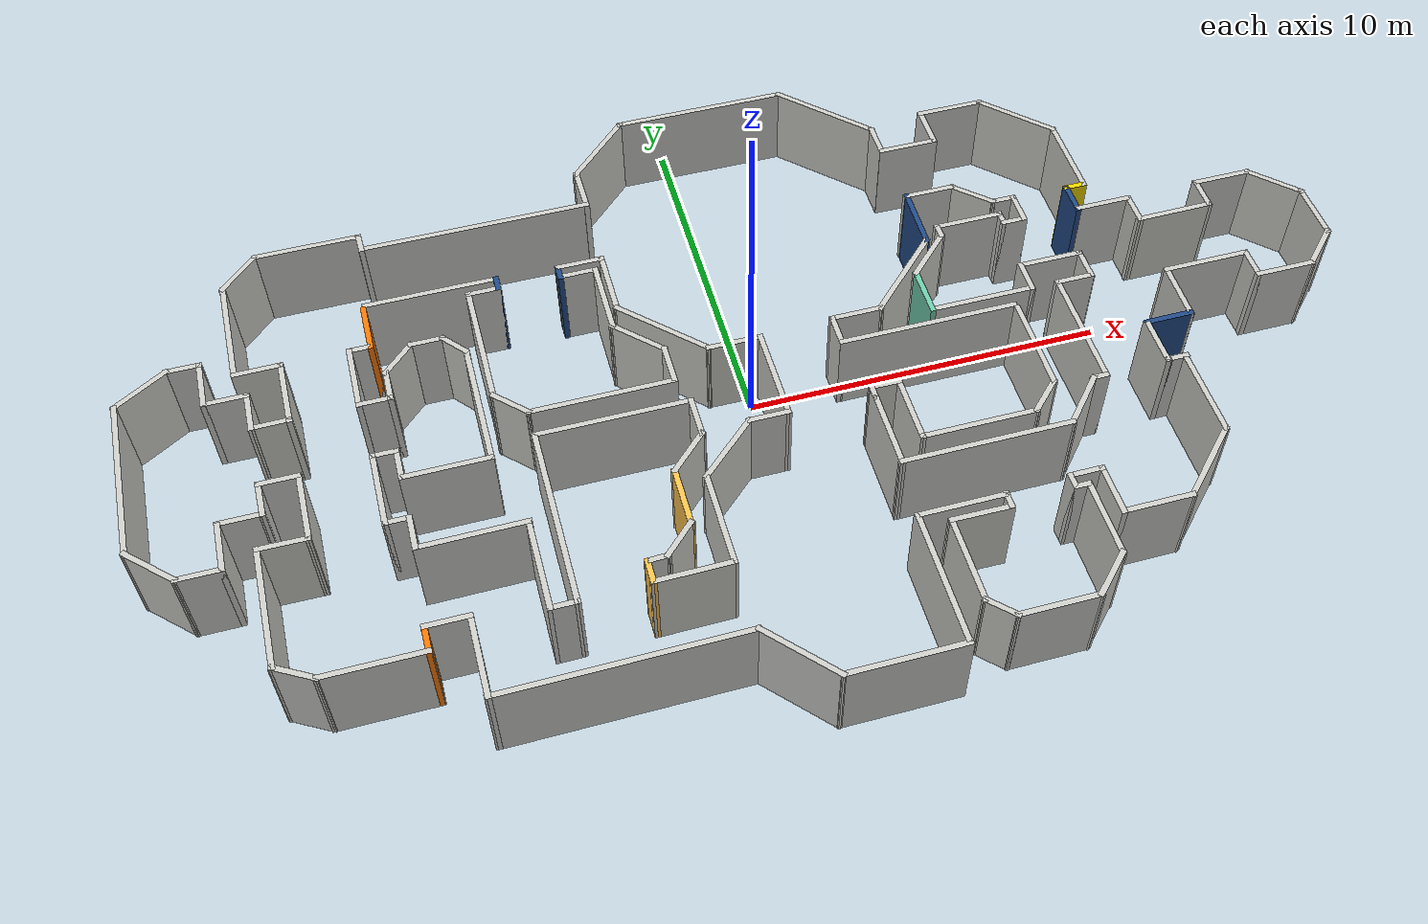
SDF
<?xml version='1.0'?>
<sdf version='1.6'>
  <model name='among_us_world'>
    <pose frame=''>0.152766 -0.289717 0 0 -0 0</pose>
    <link name='Wall_0'>
      <collision name='Wall_0_Collision'>
        <geometry>
          <box>
            <size>5 0.15 2.5</size>
          </box>
        </geometry>
        <pose frame=''>0 0 1.25 0 -0 0</pose>
      </collision>
      <visual name='Wall_0_Visual'>
        <pose frame=''>0 0 1.25 0 -0 0</pose>
        <geometry>
          <box>
            <size>5 0.15 2.5</size>
          </box>
        </geometry>
        <material>
          <script>
            <uri>file://media/materials/scripts/gazebo.material</uri>
            <name>Gazebo/CeilingTiled</name>
          </script>
          <ambient>0.12549 0.290196 0.529412 1</ambient>
        </material>
        <meta>
          <layer>0</layer>
        </meta>
      </visual>
      <pose frame=''>0.883234 9.56872 0 0 -0 0</pose>
    </link>
    <link name='Wall_1'>
      <collision name='Wall_1_Collision'>
        <geometry>
          <box>
            <size>3.25 0.15 2.5</size>
          </box>
        </geometry>
        <pose frame=''>0 0 1.25 0 -0 0</pose>
      </collision>
      <visual name='Wall_1_Visual'>
        <pose frame=''>0 0 1.25 0 -0 0</pose>
        <geometry>
          <box>
            <size>3.25 0.15 2.5</size>
          </box>
        </geometry>
        <material>
          <script>
            <uri>file://media/materials/scripts/gazebo.material</uri>
            <name>Gazebo/CeilingTiled</name>
          </script>
          <ambient>0.12549 0.290196 0.529412 1</ambient>
        </material>
        <meta>
          <layer>0</layer>
        </meta>
      </visual>
      <pose frame=''>4.40446 8.47278 0 0 -0 -0.785267</pose>
    </link>
    <link name='Wall_10'>
      <collision name='Wall_10_Collision'>
        <geometry>
          <box>
            <size>0.677967 0.15 2.5</size>
          </box>
        </geometry>
        <pose frame=''>0 0 1.25 0 -0 0</pose>
      </collision>
      <visual name='Wall_10_Visual'>
        <pose frame=''>0 0 1.25 0 -0 0</pose>
        <geometry>
          <box>
            <size>0.677967 0.15 2.5</size>
          </box>
        </geometry>
        <material>
          <script>
            <uri>file://media/materials/scripts/gazebo.material</uri>
            <name>Gazebo/Grey</name>
          </script>
          <ambient>0.929412 0.831373 0 1</ambient>
        </material>
        <meta>
          <layer>0</layer>
        </meta>
      </visual>
      <pose frame=''>10.3484 3.61514 0 0 -0 3.14159</pose>
    </link>
    <link name='Wall_101'>
      <collision name='Wall_101_Collision'>
        <geometry>
          <box>
            <size>3.75 0.15 2.5</size>
          </box>
        </geometry>
        <pose frame=''>0 0 1.25 0 -0 0</pose>
      </collision>
      <visual name='Wall_101_Visual'>
        <pose frame=''>0 0 1.25 0 -0 0</pose>
        <geometry>
          <box>
            <size>3.75 0.15 2.5</size>
          </box>
        </geometry>
        <material>
          <script>
            <uri>file://media/materials/scripts/gazebo.material</uri>
            <name>Gazebo/CeilingTiled</name>
          </script>
          <ambient>0.12549 0.290196 0.529412 1</ambient>
        </material>
        <meta>
          <layer>0</layer>
        </meta>
      </visual>
      <pose frame=''>-6.98451 2.43054 0 0 -0 -1.5708</pose>
    </link>
    <link name='Wall_103'>
      <collision name='Wall_103_Collision'>
        <geometry>
          <box>
            <size>1.25 0.15 2.5</size>
          </box>
        </geometry>
        <pose frame=''>0 0 1.25 0 -0 0</pose>
      </collision>
      <visual name='Wall_103_Visual'>
        <pose frame=''>0 0 1.25 0 -0 0</pose>
        <geometry>
          <box>
            <size>1.25 0.15 2.5</size>
          </box>
        </geometry>
        <material>
          <script>
            <uri>file://media/materials/scripts/gazebo.material</uri>
            <name>Gazebo/CeilingTiled</name>
          </script>
          <ambient>0.12549 0.290196 0.529412 1</ambient>
        </material>
        <meta>
          <layer>0</layer>
        </meta>
      </visual>
      <pose frame=''>-6.5956 0.241636 0 0 -0 -0.785398</pose>
    </link>
    <link name='Wall_104'>
      <collision name='Wall_104_Collision'>
        <geometry>
          <box>
            <size>4 0.15 2.5</size>
          </box>
        </geometry>
        <pose frame=''>0 0 1.25 0 -0 0</pose>
      </collision>
      <visual name='Wall_104_Visual'>
        <pose frame=''>0 0 1.25 0 -0 0</pose>
        <geometry>
          <box>
            <size>4 0.15 2.5</size>
          </box>
        </geometry>
        <material>
          <script>
            <uri>file://media/materials/scripts/gazebo.material</uri>
            <name>Gazebo/CeilingTiled</name>
          </script>
          <ambient>0.12549 0.290196 0.529412 1</ambient>
        </material>
        <meta>
          <layer>0</layer>
        </meta>
      </visual>
      <pose frame=''>-4.28169 -0.147272 0 0 -0 0</pose>
    </link>
    <link name='Wall_105'>
      <collision name='Wall_105_Collision'>
        <geometry>
          <box>
            <size>1.25 0.15 2.5</size>
          </box>
        </geometry>
        <pose frame=''>0 0 1.25 0 -0 0</pose>
      </collision>
      <visual name='Wall_105_Visual'>
        <pose frame=''>0 0 1.25 0 -0 0</pose>
        <geometry>
          <box>
            <size>1.25 0.15 2.5</size>
          </box>
        </geometry>
        <material>
          <script>
            <uri>file://media/materials/scripts/gazebo.material</uri>
            <name>Gazebo/CeilingTiled</name>
          </script>
          <ambient>0.12549 0.290196 0.529412 1</ambient>
        </material>
        <meta>
          <layer>0</layer>
        </meta>
      </visual>
      <pose frame=''>-2.35669 0.402728 0 0 -0 1.5708</pose>
    </link>
    <link name='Wall_106'>
      <collision name='Wall_106_Collision'>
        <geometry>
          <box>
            <size>1.75 0.15 2.5</size>
          </box>
        </geometry>
        <pose frame=''>0 0 1.25 0 -0 0</pose>
      </collision>
      <visual name='Wall_106_Visual'>
        <pose frame=''>0 0 1.25 0 -0 0</pose>
        <geometry>
          <box>
            <size>1.75 0.15 2.5</size>
          </box>
        </geometry>
        <material>
          <script>
            <uri>file://media/materials/scripts/gazebo.material</uri>
            <name>Gazebo/CeilingTiled</name>
          </script>
          <ambient>0.12549 0.290196 0.529412 1</ambient>
        </material>
        <meta>
          <layer>0</layer>
        </meta>
      </visual>
      <pose frame=''>-2.92238 1.51841 0 0 -0 2.35619</pose>
    </link>
    <link name='Wall_108'>
      <collision name='Wall_108_Collision'>
        <geometry>
          <box>
            <size>2.25 0.15 2.5</size>
          </box>
        </geometry>
        <pose frame=''>0 0 1.25 0 -0 0</pose>
      </collision>
      <visual name='Wall_108_Visual'>
        <pose frame=''>0 0 1.25 0 -0 0</pose>
        <geometry>
          <box>
            <size>2.25 0.15 2.5</size>
          </box>
        </geometry>
        <material>
          <script>
            <uri>file://media/materials/scripts/gazebo.material</uri>
            <name>Gazebo/CeilingTiled</name>
          </script>
          <ambient>0.12549 0.290196 0.529412 1</ambient>
        </material>
        <meta>
          <layer>0</layer>
        </meta>
      </visual>
      <pose frame=''>-3.48806 3.1341 0 0 -0 1.5708</pose>
    </link>
    <link name='Wall_109'>
      <collision name='Wall_109_Collision'>
        <geometry>
          <box>
            <size>1.12677 0.15 2.5</size>
          </box>
        </geometry>
        <pose frame=''>0 0 1.25 0 -0 0</pose>
      </collision>
      <visual name='Wall_109_Visual'>
        <pose frame=''>0 0 1.25 0 -0 0</pose>
        <geometry>
          <box>
            <size>1.12677 0.15 2.5</size>
          </box>
        </geometry>
        <material>
          <script>
            <uri>file://media/materials/scripts/gazebo.material</uri>
            <name>Gazebo/CeilingTiled</name>
          </script>
          <ambient>0.12549 0.290196 0.529412 1</ambient>
        </material>
        <meta>
          <layer>0</layer>
        </meta>
      </visual>
      <pose frame=''>-3.97634 4.1841 0 0 -0 3.14159</pose>
    </link>
    <link name='Wall_11'>
      <collision name='Wall_11_Collision'>
        <geometry>
          <box>
            <size>1 0.15 2.5</size>
          </box>
        </geometry>
        <pose frame=''>0 0 1.25 0 -0 0</pose>
      </collision>
      <visual name='Wall_11_Visual'>
        <pose frame=''>0 0 1.25 0 -0 0</pose>
        <geometry>
          <box>
            <size>1 0.15 2.5</size>
          </box>
        </geometry>
        <material>
          <script>
            <uri>file://media/materials/scripts/gazebo.material</uri>
            <name>Gazebo/Grey</name>
          </script>
          <ambient>0.12549 0.290196 0.529412 1</ambient>
        </material>
        <meta>
          <layer>0</layer>
        </meta>
      </visual>
      <pose frame=''>10.0844 3.17225 0 0 -0 -1.5708</pose>
    </link>
    <link name='Wall_110'>
      <collision name='Wall_110_Collision'>
        <geometry>
          <box>
            <size>0.5 0.15 2.5</size>
          </box>
        </geometry>
        <pose frame=''>0 0 1.25 0 -0 0</pose>
      </collision>
      <visual name='Wall_110_Visual'>
        <pose frame=''>0 0 1.25 0 -0 0</pose>
        <geometry>
          <box>
            <size>0.5 0.15 2.5</size>
          </box>
        </geometry>
        <material>
          <script>
            <uri>file://media/materials/scripts/gazebo.material</uri>
            <name>Gazebo/Grey</name>
          </script>
          <ambient>0.12549 0.290196 0.529412 1</ambient>
        </material>
        <meta>
          <layer>0</layer>
        </meta>
      </visual>
      <pose frame=''>-4.46462 4.33852 0 0 -0 1.5708</pose>
    </link>
    <link name='Wall_111'>
      <collision name='Wall_111_Collision'>
        <geometry>
          <box>
            <size>1.37673 0.15 2.5</size>
          </box>
        </geometry>
        <pose frame=''>0 0 1.25 0 -0 0</pose>
      </collision>
      <visual name='Wall_111_Visual'>
        <pose frame=''>0 0 1.25 0 -0 0</pose>
        <geometry>
          <box>
            <size>1.37673 0.15 2.5</size>
          </box>
        </geometry>
        <material>
          <script>
            <uri>file://media/materials/scripts/gazebo.material</uri>
            <name>Gazebo/CeilingTiled</name>
          </script>
          <ambient>0.12549 0.290196 0.529412 1</ambient>
        </material>
        <meta>
          <layer>0</layer>
        </meta>
      </visual>
      <pose frame=''>-3.85134 4.5341 0 0 -0 0</pose>
    </link>
    <link name='Wall_112'>
      <collision name='Wall_112_Collision'>
        <geometry>
          <box>
            <size>2 0.15 2.5</size>
          </box>
        </geometry>
        <pose frame=''>0 0 1.25 0 -0 0</pose>
      </collision>
      <visual name='Wall_112_Visual'>
        <pose frame=''>0 0 1.25 0 -0 0</pose>
        <geometry>
          <box>
            <size>2 0.15 2.5</size>
          </box>
        </geometry>
        <material>
          <script>
            <uri>file://media/materials/scripts/gazebo.material</uri>
            <name>Gazebo/CeilingTiled</name>
          </script>
          <ambient>0.12549 0.290196 0.529412 1</ambient>
        </material>
        <meta>
          <layer>0</layer>
        </meta>
      </visual>
      <pose frame=''>-3.23806 3.6091 0 0 -0 -1.5708</pose>
    </link>
    <link name='Wall_114'>
      <collision name='Wall_114_Collision'>
        <geometry>
          <box>
            <size>3 0.15 2.5</size>
          </box>
        </geometry>
        <pose frame=''>0 0 1.25 0 -0 0</pose>
      </collision>
      <visual name='Wall_114_Visual'>
        <pose frame=''>0 0 1.25 0 -0 0</pose>
        <geometry>
          <box>
            <size>3 0.15 2.5</size>
          </box>
        </geometry>
        <material>
          <script>
            <uri>file://media/materials/scripts/gazebo.material</uri>
            <name>Gazebo/CeilingTiled</name>
          </script>
          <ambient>0.12549 0.290196 0.529412 1</ambient>
        </material>
        <meta>
          <layer>0</layer>
        </meta>
      </visual>
      <pose frame=''>-2.23043 1.67647 0 0 -0 -0.785398</pose>
    </link>
    <link name='Wall_115'>
      <collision name='Wall_115_Collision'>
        <geometry>
          <box>
            <size>1.5655 0.15 2.5</size>
          </box>
        </geometry>
        <pose frame=''>0 0 1.25 0 -0 0</pose>
      </collision>
      <visual name='Wall_115_Visual'>
        <pose frame=''>0 0 1.25 0 -0 0</pose>
        <geometry>
          <box>
            <size>1.5655 0.15 2.5</size>
          </box>
        </geometry>
        <material>
          <script>
            <uri>file://media/materials/scripts/gazebo.material</uri>
            <name>Gazebo/CeilingTiled</name>
          </script>
          <ambient>0.12549 0.290196 0.529412 1</ambient>
        </material>
        <meta>
          <layer>0</layer>
        </meta>
      </visual>
      <pose frame=''>-0.515099 0.662156 0 0 -0 -0.00945</pose>
    </link>
    <link name='Wall_116'>
      <collision name='Wall_116_Collision'>
        <geometry>
          <box>
            <size>2.75 0.15 2.5</size>
          </box>
        </geometry>
        <pose frame=''>0 0 1.25 0 -0 0</pose>
      </collision>
      <visual name='Wall_116_Visual'>
        <pose frame=''>0 0 1.25 0 -0 0</pose>
        <geometry>
          <box>
            <size>2.75 0.15 2.5</size>
          </box>
        </geometry>
        <material>
          <script>
            <uri>file://media/materials/scripts/gazebo.material</uri>
            <name>Gazebo/CeilingTiled</name>
          </script>
          <ambient>0.12549 0.290196 0.529412 1</ambient>
        </material>
        <meta>
          <layer>0</layer>
        </meta>
      </visual>
      <pose frame=''>0.19261 -0.637844 0 0 -0 -1.5708</pose>
    </link>
    <link name='Wall_118'>
      <collision name='Wall_118_Collision'>
        <geometry>
          <box>
            <size>1.5 0.15 2.5</size>
          </box>
        </geometry>
        <pose frame=''>0 0 1.25 0 -0 0</pose>
      </collision>
      <visual name='Wall_118_Visual'>
        <pose frame=''>0 0 1.25 0 -0 0</pose>
        <geometry>
          <box>
            <size>1.5 0.15 2.5</size>
          </box>
        </geometry>
        <material>
          <script>
            <uri>file://media/materials/scripts/gazebo.material</uri>
            <name>Gazebo/CeilingTiled</name>
          </script>
          <ambient>0.12549 0.290196 0.529412 1</ambient>
        </material>
        <meta>
          <layer>0</layer>
        </meta>
      </visual>
      <pose frame=''>6.27303 4.52497 0 0 -0 0</pose>
    </link>
    <link name='Wall_119'>
      <collision name='Wall_119_Collision'>
        <geometry>
          <box>
            <size>1.41276 0.15 2.5</size>
          </box>
        </geometry>
        <pose frame=''>0 0 1.25 0 -0 0</pose>
      </collision>
      <visual name='Wall_119_Visual'>
        <pose frame=''>0 0 1.25 0 -0 0</pose>
        <geometry>
          <box>
            <size>1.41276 0.15 2.5</size>
          </box>
        </geometry>
        <material>
          <script>
            <uri>file://media/materials/scripts/gazebo.material</uri>
            <name>Gazebo/CeilingTiled</name>
          </script>
          <ambient>0.929412 0.831373 0 1</ambient>
        </material>
        <meta>
          <layer>0</layer>
        </meta>
      </visual>
      <pose frame=''>7.42533 4.09435 0 0 -0 -0.750545</pose>
    </link>
    <link name='Wall_12'>
      <collision name='Wall_12_Collision'>
        <geometry>
          <box>
            <size>1.67797 0.15 2.5</size>
          </box>
        </geometry>
        <pose frame=''>0 0 1.25 0 -0 0</pose>
      </collision>
      <visual name='Wall_12_Visual'>
        <pose frame=''>0 0 1.25 0 -0 0</pose>
        <geometry>
          <box>
            <size>1.67797 0.15 2.5</size>
          </box>
        </geometry>
        <material>
          <script>
            <uri>file://media/materials/scripts/gazebo.material</uri>
            <name>Gazebo/CeilingTiled</name>
          </script>
          <ambient>0.12549 0.290196 0.529412 1</ambient>
        </material>
        <meta>
          <layer>0</layer>
        </meta>
      </visual>
      <pose frame=''>10.8484 2.76514 0 0 -0 0</pose>
    </link>
    <link name='Wall_122'>
      <collision name='Wall_122_Collision'>
        <geometry>
          <box>
            <size>0.75 0.15 2.5</size>
          </box>
        </geometry>
        <pose frame=''>0 0 1.25 0 -0 0</pose>
      </collision>
      <visual name='Wall_122_Visual'>
        <pose frame=''>0 0 1.25 0 -0 0</pose>
        <geometry>
          <box>
            <size>0.75 0.15 2.5</size>
          </box>
        </geometry>
        <material>
          <script>
            <uri>file://media/materials/scripts/gazebo.material</uri>
            <name>Gazebo/CeilingTiled</name>
          </script>
          <ambient>0.929412 0.831373 0 1</ambient>
        </material>
        <meta>
          <layer>0</layer>
        </meta>
      </visual>
      <pose frame=''>8.18707 3.66372 0 0 -0 0</pose>
    </link>
    <link name='Wall_123'>
      <collision name='Wall_123_Collision'>
        <geometry>
          <box>
            <size>1 0.15 2.5</size>
          </box>
        </geometry>
        <pose frame=''>0 0 1.25 0 -0 0</pose>
      </collision>
      <visual name='Wall_123_Visual'>
        <pose frame=''>0 0 1.25 0 -0 0</pose>
        <geometry>
          <box>
            <size>1 0.15 2.5</size>
          </box>
        </geometry>
        <material>
          <script>
            <uri>file://media/materials/scripts/gazebo.material</uri>
            <name>Gazebo/CeilingTiled</name>
          </script>
          <ambient>0.12549 0.290196 0.529412 1</ambient>
        </material>
        <meta>
          <layer>0</layer>
        </meta>
      </visual>
      <pose frame=''>8.48707 3.23872 0 0 -0 -1.5708</pose>
    </link>
    <link name='Wall_124'>
      <collision name='Wall_124_Collision'>
        <geometry>
          <box>
            <size>0.75 0.15 2.5</size>
          </box>
        </geometry>
        <pose frame=''>0 0 1.25 0 -0 0</pose>
      </collision>
      <visual name='Wall_124_Visual'>
        <pose frame=''>0 0 1.25 0 -0 0</pose>
        <geometry>
          <box>
            <size>0.75 0.15 2.5</size>
          </box>
        </geometry>
        <material>
          <script>
            <uri>file://media/materials/scripts/gazebo.material</uri>
            <name>Gazebo/CeilingTiled</name>
          </script>
          <ambient>0.435294 0.796078 0.67451 1</ambient>
        </material>
        <meta>
          <layer>0</layer>
        </meta>
      </visual>
      <pose frame=''>8.18707 2.81372 0 0 -0 3.14159</pose>
    </link>
    <link name='Wall_125'>
      <collision name='Wall_125_Collision'>
        <geometry>
          <box>
            <size>0.5 0.15 2.5</size>
          </box>
        </geometry>
        <pose frame=''>0 0 1.25 0 -0 0</pose>
      </collision>
      <visual name='Wall_125_Visual'>
        <pose frame=''>0 0 1.25 0 -0 0</pose>
        <geometry>
          <box>
            <size>0.5 0.15 2.5</size>
          </box>
        </geometry>
        <material>
          <script>
            <uri>file://media/materials/scripts/gazebo.material</uri>
            <name>Gazebo/CeilingTiled</name>
          </script>
          <ambient>1 1 1 1</ambient>
        </material>
        <meta>
          <layer>0</layer>
        </meta>
      </visual>
      <pose frame=''>7.88707 2.98872 0 0 -0 1.5708</pose>
    </link>
    <link name='Wall_126'>
      <collision name='Wall_126_Collision'>
        <geometry>
          <box>
            <size>2 0.15 2.5</size>
          </box>
        </geometry>
        <pose frame=''>0 0 1.25 0 -0 0</pose>
      </collision>
      <visual name='Wall_126_Visual'>
        <pose frame=''>0 0 1.25 0 -0 0</pose>
        <geometry>
          <box>
            <size>2 0.15 2.5</size>
          </box>
        </geometry>
        <material>
          <script>
            <uri>file://media/materials/scripts/gazebo.material</uri>
            <name>Gazebo/CeilingTiled</name>
          </script>
          <ambient>0.435294 0.796078 0.67451 1</ambient>
        </material>
        <meta>
          <layer>0</layer>
        </meta>
      </visual>
      <pose frame=''>6.96207 3.16372 0 0 -0 3.14159</pose>
    </link>
    <link name='Wall_127'>
      <collision name='Wall_127_Collision'>
        <geometry>
          <box>
            <size>0.5 0.15 2.5</size>
          </box>
        </geometry>
        <pose frame=''>0 0 1.25 0 -0 0</pose>
      </collision>
      <visual name='Wall_127_Visual'>
        <pose frame=''>0 0 1.25 0 -0 0</pose>
        <geometry>
          <box>
            <size>0.5 0.15 2.5</size>
          </box>
        </geometry>
        <material>
          <script>
            <uri>file://media/materials/scripts/gazebo.material</uri>
            <name>Gazebo/CeilingTiled</name>
          </script>
          <ambient>0.435294 0.796078 0.67451 1</ambient>
        </material>
        <meta>
          <layer>0</layer>
        </meta>
      </visual>
      <pose frame=''>6.03707 2.98872 0 0 -0 -1.5708</pose>
    </link>
    <link name='Wall_128'>
      <collision name='Wall_128_Collision'>
        <geometry>
          <box>
            <size>1.75 0.15 2.5</size>
          </box>
        </geometry>
        <pose frame=''>0 0 1.25 0 -0 0</pose>
      </collision>
      <visual name='Wall_128_Visual'>
        <pose frame=''>0 0 1.25 0 -0 0</pose>
        <geometry>
          <box>
            <size>1.75 0.15 2.5</size>
          </box>
        </geometry>
        <material>
          <script>
            <uri>file://media/materials/scripts/gazebo.material</uri>
            <name>Gazebo/CeilingTiled</name>
          </script>
          <ambient>0.435294 0.796078 0.67451 1</ambient>
        </material>
        <meta>
          <layer>0</layer>
        </meta>
      </visual>
      <pose frame=''>5.47138 2.24804 0 0 -0 -2.35619</pose>
    </link>
    <link name='Wall_129'>
      <collision name='Wall_129_Collision'>
        <geometry>
          <box>
            <size>1.5 0.15 2.5</size>
          </box>
        </geometry>
        <pose frame=''>0 0 1.25 0 -0 0</pose>
      </collision>
      <visual name='Wall_129_Visual'>
        <pose frame=''>0 0 1.25 0 -0 0</pose>
        <geometry>
          <box>
            <size>1.5 0.15 2.5</size>
          </box>
        </geometry>
        <material>
          <script>
            <uri>file://media/materials/scripts/gazebo.material</uri>
            <name>Gazebo/Grey</name>
          </script>
          <ambient>0.435294 0.796078 0.67451 1</ambient>
        </material>
        <meta>
          <layer>0</layer>
        </meta>
      </visual>
      <pose frame=''>4.9057 1.00735 0 0 -0 -1.5708</pose>
    </link>
    <link name='Wall_13'>
      <collision name='Wall_13_Collision'>
        <geometry>
          <box>
            <size>0.99953 0.15 2.5</size>
          </box>
        </geometry>
        <pose frame=''>0 0 1.25 0 -0 0</pose>
      </collision>
      <visual name='Wall_13_Visual'>
        <pose frame=''>0 0 1.25 0 -0 0</pose>
        <geometry>
          <box>
            <size>0.99953 0.15 2.5</size>
          </box>
        </geometry>
        <material>
          <script>
            <uri>file://media/materials/scripts/gazebo.material</uri>
            <name>Gazebo/CeilingTiled</name>
          </script>
          <ambient>0.12549 0.290196 0.529412 1</ambient>
        </material>
        <meta>
          <layer>0</layer>
        </meta>
      </visual>
      <pose frame=''>11.6124 2.34037 0 0 -0 -1.5708</pose>
    </link>
    <link name='Wall_130'>
      <collision name='Wall_130_Collision'>
        <geometry>
          <box>
            <size>3 0.15 2.5</size>
          </box>
        </geometry>
        <pose frame=''>0 0 1.25 0 -0 0</pose>
      </collision>
      <visual name='Wall_130_Visual'>
        <pose frame=''>0 0 1.25 0 -0 0</pose>
        <geometry>
          <box>
            <size>3 0.15 2.5</size>
          </box>
        </geometry>
        <material>
          <script>
            <uri>file://media/materials/scripts/gazebo.material</uri>
            <name>Gazebo/CeilingTiled</name>
          </script>
          <ambient>0.435294 0.796078 0.67451 1</ambient>
        </material>
        <meta>
          <layer>0</layer>
        </meta>
      </visual>
      <pose frame=''>6.3307 0.332351 0 0 -0 0</pose>
    </link>
    <link name='Wall_131'>
      <collision name='Wall_131_Collision'>
        <geometry>
          <box>
            <size>1 0.15 2.5</size>
          </box>
        </geometry>
        <pose frame=''>0 0 1.25 0 -0 0</pose>
      </collision>
      <visual name='Wall_131_Visual'>
        <pose frame=''>0 0 1.25 0 -0 0</pose>
        <geometry>
          <box>
            <size>1 0.15 2.5</size>
          </box>
        </geometry>
        <material>
          <script>
            <uri>file://media/materials/scripts/gazebo.material</uri>
            <name>Gazebo/CeilingTiled</name>
          </script>
          <ambient>0.435294 0.796078 0.67451 1</ambient>
        </material>
        <meta>
          <layer>0</layer>
        </meta>
      </visual>
      <pose frame=''>7.7557 0.757351 0 0 -0 1.5708</pose>
    </link>
    <link name='Wall_132'>
      <collision name='Wall_132_Collision'>
        <geometry>
          <box>
            <size>1.85593 0.15 2.5</size>
          </box>
        </geometry>
        <pose frame=''>0 0 1.25 0 -0 0</pose>
      </collision>
      <visual name='Wall_132_Visual'>
        <pose frame=''>0 0 1.25 0 -0 0</pose>
        <geometry>
          <box>
            <size>1.85593 0.15 2.5</size>
          </box>
        </geometry>
        <material>
          <script>
            <uri>file://media/materials/scripts/gazebo.material</uri>
            <name>Gazebo/CeilingTiled</name>
          </script>
          <ambient>0.435294 0.796078 0.67451 1</ambient>
        </material>
        <meta>
          <layer>0</layer>
        </meta>
      </visual>
      <pose frame=''>8.60867 1.18235 0 0 -0 0</pose>
    </link>
    <link name='Wall_133'>
      <collision name='Wall_133_Collision'>
        <geometry>
          <box>
            <size>1 0.15 2.5</size>
          </box>
        </geometry>
        <pose frame=''>0 0 1.25 0 -0 0</pose>
      </collision>
      <visual name='Wall_133_Visual'>
        <pose frame=''>0 0 1.25 0 -0 0</pose>
        <geometry>
          <box>
            <size>1 0.15 2.5</size>
          </box>
        </geometry>
        <material>
          <script>
            <uri>file://media/materials/scripts/gazebo.material</uri>
            <name>Gazebo/CeilingTiled</name>
          </script>
          <ambient>0.12549 0.290196 0.529412 1</ambient>
        </material>
        <meta>
          <layer>0</layer>
        </meta>
      </visual>
      <pose frame=''>9.47952 0.757351 0 0 -0 -1.5708</pose>
    </link>
    <link name='Wall_134'>
      <collision name='Wall_134_Collision'>
        <geometry>
          <box>
            <size>1.10593 0.15 2.5</size>
          </box>
        </geometry>
        <pose frame=''>0 0 1.25 0 -0 0</pose>
      </collision>
      <visual name='Wall_134_Visual'>
        <pose frame=''>0 0 1.25 0 -0 0</pose>
        <geometry>
          <box>
            <size>1.10593 0.15 2.5</size>
          </box>
        </geometry>
        <material>
          <script>
            <uri>file://media/materials/scripts/gazebo.material</uri>
            <name>Gazebo/CeilingTiled</name>
          </script>
          <ambient>0.12549 0.290196 0.529412 1</ambient>
        </material>
        <meta>
          <layer>0</layer>
        </meta>
      </visual>
      <pose frame=''>8.98367 0.332351 0 0 -0 3.14159</pose>
    </link>
    <link name='Wall_135'>
      <collision name='Wall_135_Collision'>
        <geometry>
          <box>
            <size>3.5 0.15 2.5</size>
          </box>
        </geometry>
        <pose frame=''>0 0 1.25 0 -0 0</pose>
      </collision>
      <visual name='Wall_135_Visual'>
        <pose frame=''>0 0 1.25 0 -0 0</pose>
        <geometry>
          <box>
            <size>3.5 0.15 2.5</size>
          </box>
        </geometry>
        <material>
          <script>
            <uri>file://media/materials/scripts/gazebo.material</uri>
            <name>Gazebo/CeilingTiled</name>
          </script>
          <ambient>0.12549 0.290196 0.529412 1</ambient>
        </material>
        <meta>
          <layer>0</layer>
        </meta>
      </visual>
      <pose frame=''>8.5057 -1.34265 0 0 -0 -1.5708</pose>
    </link>
    <link name='Wall_136'>
      <collision name='Wall_136_Collision'>
        <geometry>
          <box>
            <size>0.5 0.15 2.5</size>
          </box>
        </geometry>
        <pose frame=''>0 0 1.25 0 -0 0</pose>
      </collision>
      <visual name='Wall_136_Visual'>
        <pose frame=''>0 0 1.25 0 -0 0</pose>
        <geometry>
          <box>
            <size>0.5 0.15 2.5</size>
          </box>
        </geometry>
        <material>
          <script>
            <uri>file://media/materials/scripts/gazebo.material</uri>
            <name>Gazebo/CeilingTiled</name>
          </script>
          <ambient>0.929412 0.831373 0 1</ambient>
        </material>
        <meta>
          <layer>0</layer>
        </meta>
      </visual>
      <pose frame=''>8.3307 -3.01765 0 0 -0 3.14159</pose>
    </link>
    <link name='Wall_14'>
      <collision name='Wall_14_Collision'>
        <geometry>
          <box>
            <size>2.25007 0.15 2.5</size>
          </box>
        </geometry>
        <pose frame=''>0 0 1.25 0 -0 0</pose>
      </collision>
      <visual name='Wall_14_Visual'>
        <pose frame=''>0 0 1.25 0 -0 0</pose>
        <geometry>
          <box>
            <size>2.25007 0.15 2.5</size>
          </box>
        </geometry>
        <material>
          <script>
            <uri>file://media/materials/scripts/gazebo.material</uri>
            <name>Gazebo/CeilingTiled</name>
          </script>
          <ambient>0.12549 0.290196 0.529412 1</ambient>
        </material>
        <meta>
          <layer>0</layer>
        </meta>
      </visual>
      <pose frame=''>12.6445 1.92431 0 0 -0 0.008281</pose>
    </link>
    <link name='Wall_141'>
      <collision name='Wall_141_Collision'>
        <geometry>
          <box>
            <size>4.75 0.15 2.5</size>
          </box>
        </geometry>
        <pose frame=''>0 0 1.25 0 -0 0</pose>
      </collision>
      <visual name='Wall_141_Visual'>
        <pose frame=''>0 0 1.25 0 -0 0</pose>
        <geometry>
          <box>
            <size>4.75 0.15 2.5</size>
          </box>
        </geometry>
        <material>
          <script>
            <uri>file://media/materials/scripts/gazebo.material</uri>
            <name>Gazebo/CeilingTiled</name>
          </script>
          <ambient>0.12549 0.290196 0.529412 1</ambient>
        </material>
        <meta>
          <layer>0</layer>
        </meta>
      </visual>
      <pose frame=''>4.78856 -4.21327 0 0 -0 0</pose>
    </link>
    <link name='Wall_143'>
      <collision name='Wall_143_Collision'>
        <geometry>
          <box>
            <size>1.75259 0.15 2.5</size>
          </box>
        </geometry>
        <pose frame=''>0 0 1.25 0 -0 0</pose>
      </collision>
      <visual name='Wall_143_Visual'>
        <pose frame=''>0 0 1.25 0 -0 0</pose>
        <geometry>
          <box>
            <size>1.75259 0.15 2.5</size>
          </box>
        </geometry>
        <material>
          <script>
            <uri>file://media/materials/scripts/gazebo.material</uri>
            <name>Gazebo/CeilingTiled</name>
          </script>
          <ambient>0.929412 0.831373 0 1</ambient>
        </material>
        <meta>
          <layer>0</layer>
        </meta>
      </visual>
      <pose frame=''>7.62213 -3.61546 0 0 -0 -2.29947</pose>
    </link>
    <link name='Wall_145'>
      <collision name='Wall_145_Collision'>
        <geometry>
          <box>
            <size>5.25 0.15 2.5</size>
          </box>
        </geometry>
        <pose frame=''>0 0 1.25 0 -0 0</pose>
      </collision>
      <visual name='Wall_145_Visual'>
        <pose frame=''>0 0 1.25 0 -0 0</pose>
        <geometry>
          <box>
            <size>5.25 0.15 2.5</size>
          </box>
        </geometry>
        <material>
          <script>
            <uri>file://media/materials/scripts/gazebo.material</uri>
            <name>Gazebo/CeilingTiled</name>
          </script>
          <ambient>1 0.764706 0.305882 1</ambient>
        </material>
        <meta>
          <layer>0</layer>
        </meta>
      </visual>
      <pose frame=''>-6.21277 -3.45528 0 0 -0 1.5708</pose>
    </link>
    <link name='Wall_146'>
      <collision name='Wall_146_Collision'>
        <geometry>
          <box>
            <size>4.25 0.15 2.5</size>
          </box>
        </geometry>
        <pose frame=''>0 0 1.25 0 -0 0</pose>
      </collision>
      <visual name='Wall_146_Visual'>
        <pose frame=''>0 0 1.25 0 -0 0</pose>
        <geometry>
          <box>
            <size>4.25 0.15 2.5</size>
          </box>
        </geometry>
        <material>
          <script>
            <uri>file://media/materials/scripts/gazebo.material</uri>
            <name>Gazebo/CeilingTiled</name>
          </script>
          <ambient>1 0.764706 0.305882 1</ambient>
        </material>
        <meta>
          <layer>0</layer>
        </meta>
      </visual>
      <pose frame=''>-4.16277 -0.905283 0 0 -0 0</pose>
    </link>
    <link name='Wall_147'>
      <collision name='Wall_147_Collision'>
        <geometry>
          <box>
            <size>1.25 0.15 2.5</size>
          </box>
        </geometry>
        <pose frame=''>0 0 1.25 0 -0 0</pose>
      </collision>
      <visual name='Wall_147_Visual'>
        <pose frame=''>0 0 1.25 0 -0 0</pose>
        <geometry>
          <box>
            <size>1.25 0.15 2.5</size>
          </box>
        </geometry>
        <material>
          <script>
            <uri>file://media/materials/scripts/gazebo.material</uri>
            <name>Gazebo/CeilingTiled</name>
          </script>
          <ambient>1 0.764706 0.305882 1</ambient>
        </material>
        <meta>
          <layer>0</layer>
        </meta>
      </visual>
      <pose frame=''>-2.11277 -1.45528 0 0 -0 -1.5708</pose>
    </link>
    <link name='Wall_148'>
      <collision name='Wall_148_Collision'>
        <geometry>
          <box>
            <size>1.5 0.15 2.5</size>
          </box>
        </geometry>
        <pose frame=''>0 0 1.25 0 -0 0</pose>
      </collision>
      <visual name='Wall_148_Visual'>
        <pose frame=''>0 0 1.25 0 -0 0</pose>
        <geometry>
          <box>
            <size>1.5 0.15 2.5</size>
          </box>
        </geometry>
        <material>
          <script>
            <uri>file://media/materials/scripts/gazebo.material</uri>
            <name>Gazebo/CeilingTiled</name>
          </script>
          <ambient>1 0.764706 0.305882 1</ambient>
        </material>
        <meta>
          <layer>0</layer>
        </meta>
      </visual>
      <pose frame=''>-2.59027 -2.48228 0 0 -0 -2.35672</pose>
    </link>
    <link name='Wall_149'>
      <collision name='Wall_149_Collision'>
        <geometry>
          <box>
            <size>1.75 0.15 2.5</size>
          </box>
        </geometry>
        <pose frame=''>0 0 1.25 0 -0 0</pose>
      </collision>
      <visual name='Wall_149_Visual'>
        <pose frame=''>0 0 1.25 0 -0 0</pose>
        <geometry>
          <box>
            <size>1.75 0.15 2.5</size>
          </box>
        </geometry>
        <material>
          <script>
            <uri>file://media/materials/scripts/gazebo.material</uri>
            <name>Gazebo/Grey</name>
          </script>
          <ambient>1 0.764706 0.305882 1</ambient>
        </material>
        <meta>
          <layer>0</layer>
        </meta>
      </visual>
      <pose frame=''>-3.06777 -3.75928 0 0 -0 -1.5708</pose>
    </link>
    <link name='Wall_15'>
      <collision name='Wall_15_Collision'>
        <geometry>
          <box>
            <size>1.02562 0.15 2.5</size>
          </box>
        </geometry>
        <pose frame=''>0 0 1.25 0 -0 0</pose>
      </collision>
      <visual name='Wall_15_Visual'>
        <pose frame=''>0 0 1.25 0 -0 0</pose>
        <geometry>
          <box>
            <size>1.02562 0.15 2.5</size>
          </box>
        </geometry>
        <material>
          <script>
            <uri>file://media/materials/scripts/gazebo.material</uri>
            <name>Gazebo/CeilingTiled</name>
          </script>
          <ambient>0.180392 0.203922 0.211765 1</ambient>
        </material>
        <meta>
          <layer>0</layer>
        </meta>
      </visual>
      <pose frame=''>13.7124 2.37081 0 0 -0 1.5708</pose>
    </link>
    <link name='Wall_150'>
      <collision name='Wall_150_Collision'>
        <geometry>
          <box>
            <size>1.25 0.15 2.5</size>
          </box>
        </geometry>
        <pose frame=''>0 0 1.25 0 -0 0</pose>
      </collision>
      <visual name='Wall_150_Visual'>
        <pose frame=''>0 0 1.25 0 -0 0</pose>
        <geometry>
          <box>
            <size>1.25 0.15 2.5</size>
          </box>
        </geometry>
        <material>
          <script>
            <uri>file://media/materials/scripts/gazebo.material</uri>
            <name>Gazebo/CeilingTiled</name>
          </script>
          <ambient>1 0.764706 0.305882 1</ambient>
        </material>
        <meta>
          <layer>0</layer>
        </meta>
      </visual>
      <pose frame=''>-3.45677 -4.94828 0 0 -0 -2.35619</pose>
    </link>
    <link name='Wall_153'>
      <collision name='Wall_153_Collision'>
        <geometry>
          <box>
            <size>0.660076 0.15 2.5</size>
          </box>
        </geometry>
        <pose frame=''>0 0 1.25 0 -0 0</pose>
      </collision>
      <visual name='Wall_153_Visual'>
        <pose frame=''>0 0 1.25 0 -0 0</pose>
        <geometry>
          <box>
            <size>0.660076 0.15 2.5</size>
          </box>
        </geometry>
        <material>
          <script>
            <uri>file://media/materials/scripts/gazebo.material</uri>
            <name>Gazebo/CeilingTiled</name>
          </script>
          <ambient>1 0.764706 0.305882 1</ambient>
        </material>
        <meta>
          <layer>0</layer>
        </meta>
      </visual>
      <pose frame=''>-4.10077 -5.34628 0 0 -0 -3.10631</pose>
    </link>
    <link name='Wall_154'>
      <collision name='Wall_154_Collision'>
        <geometry>
          <box>
            <size>0.75 0.15 2.5</size>
          </box>
        </geometry>
        <pose frame=''>0 0 1.25 0 -0 0</pose>
      </collision>
      <visual name='Wall_154_Visual'>
        <pose frame=''>0 0 1.25 0 -0 0</pose>
        <geometry>
          <box>
            <size>0.75 0.15 2.5</size>
          </box>
        </geometry>
        <material>
          <script>
            <uri>file://media/materials/scripts/gazebo.material</uri>
            <name>Gazebo/Grey</name>
          </script>
          <ambient>1 0.764706 0.305882 1</ambient>
        </material>
        <meta>
          <layer>0</layer>
        </meta>
      </visual>
      <pose frame=''>-4.35577 -5.65528 0 0 -0 -1.5708</pose>
    </link>
    <link name='Wall_155'>
      <collision name='Wall_155_Collision'>
        <geometry>
          <box>
            <size>2.16008 0.15 2.5</size>
          </box>
        </geometry>
        <pose frame=''>0 0 1.25 0 -0 0</pose>
      </collision>
      <visual name='Wall_155_Visual'>
        <pose frame=''>0 0 1.25 0 -0 0</pose>
        <geometry>
          <box>
            <size>2.16008 0.15 2.5</size>
          </box>
        </geometry>
        <material>
          <script>
            <uri>file://media/materials/scripts/gazebo.material</uri>
            <name>Gazebo/CeilingTiled</name>
          </script>
          <ambient>0.12549 0.290196 0.529412 1</ambient>
        </material>
        <meta>
          <layer>0</layer>
        </meta>
      </visual>
      <pose frame=''>-3.35065 -5.9463 0 0 -0 0.008937</pose>
    </link>
    <link name='Wall_156'>
      <collision name='Wall_156_Collision'>
        <geometry>
          <box>
            <size>2.75 0.15 2.5</size>
          </box>
        </geometry>
        <pose frame=''>0 0 1.25 0 -0 0</pose>
      </collision>
      <visual name='Wall_156_Visual'>
        <pose frame=''>0 0 1.25 0 -0 0</pose>
        <geometry>
          <box>
            <size>2.75 0.15 2.5</size>
          </box>
        </geometry>
        <material>
          <script>
            <uri>file://media/materials/scripts/gazebo.material</uri>
            <name>Gazebo/CeilingTiled</name>
          </script>
          <ambient>0.333333 0.341176 0.32549 1</ambient>
        </material>
        <meta>
          <layer>0</layer>
        </meta>
      </visual>
      <pose frame=''>-2.34553 -4.63732 0 0 -0 1.5708</pose>
    </link>
    <link name='Wall_160'>
      <collision name='Wall_160_Collision'>
        <geometry>
          <box>
            <size>0.797757 0.15 2.5</size>
          </box>
        </geometry>
        <pose frame=''>0 0 1.25 0 -0 0</pose>
      </collision>
      <visual name='Wall_160_Visual'>
        <pose frame=''>0 0 1.25 0 -0 0</pose>
        <geometry>
          <box>
            <size>0.797757 0.15 2.5</size>
          </box>
        </geometry>
        <material>
          <script>
            <uri>file://media/materials/scripts/gazebo.material</uri>
            <name>Gazebo/CeilingTiled</name>
          </script>
          <ambient>0.12549 0.290196 0.529412 1</ambient>
        </material>
        <meta>
          <layer>0</layer>
        </meta>
      </visual>
      <pose frame=''>-6.53682 -6.00509 0 0 -0 3.14101</pose>
    </link>
    <link name='Wall_161'>
      <collision name='Wall_161_Collision'>
        <geometry>
          <box>
            <size>2.70224 0.15 2.5</size>
          </box>
        </geometry>
        <pose frame=''>0 0 1.25 0 -0 0</pose>
      </collision>
      <visual name='Wall_161_Visual'>
        <pose frame=''>0 0 1.25 0 -0 0</pose>
        <geometry>
          <box>
            <size>2.70224 0.15 2.5</size>
          </box>
        </geometry>
        <material>
          <script>
            <uri>file://media/materials/scripts/gazebo.material</uri>
            <name>Gazebo/CeilingTiled</name>
          </script>
          <ambient>0.12549 0.290196 0.529412 1</ambient>
        </material>
        <meta>
          <layer>0</layer>
        </meta>
      </visual>
      <pose frame=''>-6.87644 -4.72879 0 0 -0 1.5708</pose>
    </link>
    <link name='Wall_162'>
      <collision name='Wall_162_Collision'>
        <geometry>
          <box>
            <size>2.95229 0.15 2.5</size>
          </box>
        </geometry>
        <pose frame=''>0 0 1.25 0 -0 0</pose>
      </collision>
      <visual name='Wall_162_Visual'>
        <pose frame=''>0 0 1.25 0 -0 0</pose>
        <geometry>
          <box>
            <size>2.95229 0.15 2.5</size>
          </box>
        </geometry>
        <material>
          <script>
            <uri>file://media/materials/scripts/gazebo.material</uri>
            <name>Gazebo/CeilingTiled</name>
          </script>
          <ambient>0.12549 0.290196 0.529412 1</ambient>
        </material>
        <meta>
          <layer>0</layer>
        </meta>
      </visual>
      <pose frame=''>-8.262 -3.46044 0 0 -0 -3.13604</pose>
    </link>
    <link name='Wall_163'>
      <collision name='Wall_163_Collision'>
        <geometry>
          <box>
            <size>1.04776 0.15 2.5</size>
          </box>
        </geometry>
        <pose frame=''>0 0 1.25 0 -0 0</pose>
      </collision>
      <visual name='Wall_163_Visual'>
        <pose frame=''>0 0 1.25 0 -0 0</pose>
        <geometry>
          <box>
            <size>1.04776 0.15 2.5</size>
          </box>
        </geometry>
        <material>
          <script>
            <uri>file://media/materials/scripts/gazebo.material</uri>
            <name>Gazebo/CeilingTiled</name>
          </script>
          <ambient>0.996078 0.47451 0.0196078 1</ambient>
        </material>
        <meta>
          <layer>0</layer>
        </meta>
      </visual>
      <pose frame=''>-9.66312 -3.00378 0 0 -0 1.5708</pose>
    </link>
    <link name='Wall_164'>
      <collision name='Wall_164_Collision'>
        <geometry>
          <box>
            <size>0.75 0.15 2.5</size>
          </box>
        </geometry>
        <pose frame=''>0 0 1.25 0 -0 0</pose>
      </collision>
      <visual name='Wall_164_Visual'>
        <pose frame=''>0 0 1.25 0 -0 0</pose>
        <geometry>
          <box>
            <size>0.75 0.15 2.5</size>
          </box>
        </geometry>
        <material>
          <script>
            <uri>file://media/materials/scripts/gazebo.material</uri>
            <name>Gazebo/CeilingTiled</name>
          </script>
          <ambient>0.996078 0.47451 0.0196078 1</ambient>
        </material>
        <meta>
          <layer>0</layer>
        </meta>
      </visual>
      <pose frame=''>-9.96312 -2.55491 0 0 -0 3.14159</pose>
    </link>
    <link name='Wall_165'>
      <collision name='Wall_165_Collision'>
        <geometry>
          <box>
            <size>2.25 0.15 2.5</size>
          </box>
        </geometry>
        <pose frame=''>0 0 1.25 0 -0 0</pose>
      </collision>
      <visual name='Wall_165_Visual'>
        <pose frame=''>0 0 1.25 0 -0 0</pose>
        <geometry>
          <box>
            <size>2.25 0.15 2.5</size>
          </box>
        </geometry>
        <material>
          <script>
            <uri>file://media/materials/scripts/gazebo.material</uri>
            <name>Gazebo/CeilingTiled</name>
          </script>
          <ambient>0.12549 0.290196 0.529412 1</ambient>
        </material>
        <meta>
          <layer>0</layer>
        </meta>
      </visual>
      <pose frame=''>-10.2631 -1.50491 0 0 -0 1.5708</pose>
    </link>
    <link name='Wall_166'>
      <collision name='Wall_166_Collision'>
        <geometry>
          <box>
            <size>0.75 0.15 2.5</size>
          </box>
        </geometry>
        <pose frame=''>0 0 1.25 0 -0 0</pose>
      </collision>
      <visual name='Wall_166_Visual'>
        <pose frame=''>0 0 1.25 0 -0 0</pose>
        <geometry>
          <box>
            <size>0.75 0.15 2.5</size>
          </box>
        </geometry>
        <material>
          <script>
            <uri>file://media/materials/scripts/gazebo.material</uri>
            <name>Gazebo/CeilingTiled</name>
          </script>
          <ambient>0.435294 0.796078 0.67451 1</ambient>
        </material>
        <meta>
          <layer>0</layer>
        </meta>
      </visual>
      <pose frame=''>-9.96312 -0.454906 0 0 -0 0</pose>
    </link>
    <link name='Wall_167'>
      <collision name='Wall_167_Collision'>
        <geometry>
          <box>
            <size>1 0.15 2.5</size>
          </box>
        </geometry>
        <pose frame=''>0 0 1.25 0 -0 0</pose>
      </collision>
      <visual name='Wall_167_Visual'>
        <pose frame=''>0 0 1.25 0 -0 0</pose>
        <geometry>
          <box>
            <size>1 0.15 2.5</size>
          </box>
        </geometry>
        <material>
          <script>
            <uri>file://media/materials/scripts/gazebo.material</uri>
            <name>Gazebo/CeilingTiled</name>
          </script>
          <ambient>0.435294 0.796078 0.67451 1</ambient>
        </material>
        <meta>
          <layer>0</layer>
        </meta>
      </visual>
      <pose frame=''>-9.66312 -0.879906 0 0 -0 -1.5708</pose>
    </link>
    <link name='Wall_168'>
      <collision name='Wall_168_Collision'>
        <geometry>
          <box>
            <size>2.40666 0.15 2.5</size>
          </box>
        </geometry>
        <pose frame=''>0 0 1.25 0 -0 0</pose>
      </collision>
      <visual name='Wall_168_Visual'>
        <pose frame=''>0 0 1.25 0 -0 0</pose>
        <geometry>
          <box>
            <size>2.40666 0.15 2.5</size>
          </box>
        </geometry>
        <material>
          <script>
            <uri>file://media/materials/scripts/gazebo.material</uri>
            <name>Gazebo/CeilingTiled</name>
          </script>
          <ambient>0.435294 0.796078 0.67451 1</ambient>
        </material>
        <meta>
          <layer>0</layer>
        </meta>
      </visual>
      <pose frame=''>-8.53479 -1.30491 0 0 -0 0</pose>
    </link>
    <link name='Wall_169'>
      <collision name='Wall_169_Collision'>
        <geometry>
          <box>
            <size>3.75 0.15 2.5</size>
          </box>
        </geometry>
        <pose frame=''>0 0 1.25 0 -0 0</pose>
      </collision>
      <visual name='Wall_169_Visual'>
        <pose frame=''>0 0 1.25 0 -0 0</pose>
        <geometry>
          <box>
            <size>3.75 0.15 2.5</size>
          </box>
        </geometry>
        <material>
          <script>
            <uri>file://media/materials/scripts/gazebo.material</uri>
            <name>Gazebo/CeilingTiled</name>
          </script>
          <ambient>0.435294 0.796078 0.67451 1</ambient>
        </material>
        <meta>
          <layer>0</layer>
        </meta>
      </visual>
      <pose frame=''>-7.39091 0.495094 0 0 -0 1.5708</pose>
    </link>
    <link name='Wall_170'>
      <collision name='Wall_170_Collision'>
        <geometry>
          <box>
            <size>0.93677 0.15 2.5</size>
          </box>
        </geometry>
        <pose frame=''>0 0 1.25 0 -0 0</pose>
      </collision>
      <visual name='Wall_170_Visual'>
        <pose frame=''>0 0 1.25 0 -0 0</pose>
        <geometry>
          <box>
            <size>0.93677 0.15 2.5</size>
          </box>
        </geometry>
        <material>
          <script>
            <uri>file://media/materials/scripts/gazebo.material</uri>
            <name>Gazebo/CeilingTiled</name>
          </script>
          <ambient>0.435294 0.796078 0.67451 1</ambient>
        </material>
        <meta>
          <layer>0</layer>
        </meta>
      </visual>
      <pose frame=''>-7.66031 2.59561 0 0 -0 2.2722</pose>
    </link>
    <link name='Wall_171'>
      <collision name='Wall_171_Collision'>
        <geometry>
          <box>
            <size>1 0.15 2.5</size>
          </box>
        </geometry>
        <pose frame=''>0 0 1.25 0 -0 0</pose>
      </collision>
      <visual name='Wall_171_Visual'>
        <pose frame=''>0 0 1.25 0 -0 0</pose>
        <geometry>
          <box>
            <size>1 0.15 2.5</size>
          </box>
        </geometry>
        <material>
          <script>
            <uri>file://media/materials/scripts/gazebo.material</uri>
            <name>Gazebo/CeilingTiled</name>
          </script>
          <ambient>0.435294 0.796078 0.67451 1</ambient>
        </material>
        <meta>
          <layer>0</layer>
        </meta>
      </visual>
      <pose frame=''>-8.33916 2.89614 0 0 -0 3.14159</pose>
    </link>
    <link name='Wall_172'>
      <collision name='Wall_172_Collision'>
        <geometry>
          <box>
            <size>1.25 0.15 2.5</size>
          </box>
        </geometry>
        <pose frame=''>0 0 1.25 0 -0 0</pose>
      </collision>
      <visual name='Wall_172_Visual'>
        <pose frame=''>0 0 1.25 0 -0 0</pose>
        <geometry>
          <box>
            <size>1.25 0.15 2.5</size>
          </box>
        </geometry>
        <material>
          <script>
            <uri>file://media/materials/scripts/gazebo.material</uri>
            <name>Gazebo/CeilingTiled</name>
          </script>
          <ambient>0.435294 0.796078 0.67451 1</ambient>
        </material>
        <meta>
          <layer>0</layer>
        </meta>
      </visual>
      <pose frame=''>-9.15307 2.50723 0 0 -0 -2.35619</pose>
    </link>
    <link name='Wall_173'>
      <collision name='Wall_173_Collision'>
        <geometry>
          <box>
            <size>1 0.15 2.5</size>
          </box>
        </geometry>
        <pose frame=''>0 0 1.25 0 -0 0</pose>
      </collision>
      <visual name='Wall_173_Visual'>
        <pose frame=''>0 0 1.25 0 -0 0</pose>
        <geometry>
          <box>
            <size>1 0.15 2.5</size>
          </box>
        </geometry>
        <material>
          <script>
            <uri>file://media/materials/scripts/gazebo.material</uri>
            <name>Gazebo/CeilingTiled</name>
          </script>
          <ambient>0.435294 0.796078 0.67451 1</ambient>
        </material>
        <meta>
          <layer>0</layer>
        </meta>
      </visual>
      <pose frame=''>-9.54198 1.69332 0 0 -0 -1.5708</pose>
    </link>
    <link name='Wall_174'>
      <collision name='Wall_174_Collision'>
        <geometry>
          <box>
            <size>0.969112 0.15 2.5</size>
          </box>
        </geometry>
        <pose frame=''>0 0 1.25 0 -0 0</pose>
      </collision>
      <visual name='Wall_174_Visual'>
        <pose frame=''>0 0 1.25 0 -0 0</pose>
        <geometry>
          <box>
            <size>0.969112 0.15 2.5</size>
          </box>
        </geometry>
        <material>
          <script>
            <uri>file://media/materials/scripts/gazebo.material</uri>
            <name>Gazebo/CeilingTiled</name>
          </script>
          <ambient>0.435294 0.796078 0.67451 1</ambient>
        </material>
        <meta>
          <layer>0</layer>
        </meta>
      </visual>
      <pose frame=''>-9.95154 1.26832 0 0 -0 -3.14159</pose>
    </link>
    <link name='Wall_175'>
      <collision name='Wall_175_Collision'>
        <geometry>
          <box>
            <size>2 0.15 2.5</size>
          </box>
        </geometry>
        <pose frame=''>0 0 1.25 0 -0 0</pose>
      </collision>
      <visual name='Wall_175_Visual'>
        <pose frame=''>0 0 1.25 0 -0 0</pose>
        <geometry>
          <box>
            <size>2 0.15 2.5</size>
          </box>
        </geometry>
        <material>
          <script>
            <uri>file://media/materials/scripts/gazebo.material</uri>
            <name>Gazebo/CeilingTiled</name>
          </script>
          <ambient>0.12549 0.290196 0.529412 1</ambient>
        </material>
        <meta>
          <layer>0</layer>
        </meta>
      </visual>
      <pose frame=''>-10.3611 2.17994 0 0 -0 1.5708</pose>
    </link>
    <link name='Wall_176'>
      <collision name='Wall_176_Collision'>
        <geometry>
          <box>
            <size>0.719112 0.15 2.5</size>
          </box>
        </geometry>
        <pose frame=''>0 0 1.25 0 -0 0</pose>
      </collision>
      <visual name='Wall_176_Visual'>
        <pose frame=''>0 0 1.25 0 -0 0</pose>
        <geometry>
          <box>
            <size>0.719112 0.15 2.5</size>
          </box>
        </geometry>
        <material>
          <script>
            <uri>file://media/materials/scripts/gazebo.material</uri>
            <name>Gazebo/CeilingTiled</name>
          </script>
          <ambient>0.996078 0.47451 0.0196078 1</ambient>
        </material>
        <meta>
          <layer>0</layer>
        </meta>
      </visual>
      <pose frame=''>-10.0765 3.11832 0 0 -0 0</pose>
    </link>
    <link name='Wall_177'>
      <collision name='Wall_177_Collision'>
        <geometry>
          <box>
            <size>1.5 0.15 2.5</size>
          </box>
        </geometry>
        <pose frame=''>0 0 1.25 0 -0 0</pose>
      </collision>
      <visual name='Wall_177_Visual'>
        <pose frame=''>0 0 1.25 0 -0 0</pose>
        <geometry>
          <box>
            <size>1.5 0.15 2.5</size>
          </box>
        </geometry>
        <material>
          <script>
            <uri>file://media/materials/scripts/gazebo.material</uri>
            <name>Gazebo/Grey</name>
          </script>
          <ambient>0.996078 0.47451 0.0196078 1</ambient>
        </material>
        <meta>
          <layer>0</layer>
        </meta>
      </visual>
      <pose frame=''>-9.79198 3.79332 0 0 -0 1.5708</pose>
    </link>
    <link name='Wall_179'>
      <collision name='Wall_179_Collision'>
        <geometry>
          <box>
            <size>1.90693 0.15 2.5</size>
          </box>
        </geometry>
        <pose frame=''>0 0 1.25 0 -0 0</pose>
      </collision>
      <visual name='Wall_179_Visual'>
        <pose frame=''>0 0 1.25 0 -0 0</pose>
        <geometry>
          <box>
            <size>1.90693 0.15 2.5</size>
          </box>
        </geometry>
        <material>
          <script>
            <uri>file://media/materials/scripts/gazebo.material</uri>
            <name>Gazebo/Grey</name>
          </script>
          <ambient>0.12549 0.290196 0.529412 1</ambient>
        </material>
        <meta>
          <layer>0</layer>
        </meta>
      </visual>
      <pose frame=''>5.59803 3.64664 0 0 -0 -1.58851</pose>
    </link>
    <link name='Wall_180'>
      <collision name='Wall_180_Collision'>
        <geometry>
          <box>
            <size>3 0.15 2.5</size>
          </box>
        </geometry>
        <pose frame=''>0 0 1.25 0 -0 0</pose>
      </collision>
      <visual name='Wall_180_Visual'>
        <pose frame=''>0 0 1.25 0 -0 0</pose>
        <geometry>
          <box>
            <size>3 0.15 2.5</size>
          </box>
        </geometry>
        <material>
          <script>
            <uri>file://media/materials/scripts/gazebo.material</uri>
            <name>Gazebo/CeilingTiled</name>
          </script>
          <ambient>0.12549 0.290196 0.529412 1</ambient>
        </material>
        <meta>
          <layer>0</layer>
        </meta>
      </visual>
      <pose frame=''>4.57485 1.76069 0 0 -0 -2.35619</pose>
    </link>
    <link name='Wall_183'>
      <collision name='Wall_183_Collision'>
        <geometry>
          <box>
            <size>1.5 0.15 2.5</size>
          </box>
        </geometry>
        <pose frame=''>0 0 1.25 0 -0 0</pose>
      </collision>
      <visual name='Wall_183_Visual'>
        <pose frame=''>0 0 1.25 0 -0 0</pose>
        <geometry>
          <box>
            <size>1.5 0.15 2.5</size>
          </box>
        </geometry>
        <material>
          <script>
            <uri>file://media/materials/scripts/gazebo.material</uri>
            <name>Gazebo/CeilingTiled</name>
          </script>
          <ambient>0.12549 0.290196 0.529412 1</ambient>
        </material>
        <meta>
          <layer>0</layer>
        </meta>
      </visual>
      <pose frame=''>2.89222 0.753062 0 0 -0 3.14159</pose>
    </link>
    <link name='Wall_184'>
      <collision name='Wall_184_Collision'>
        <geometry>
          <box>
            <size>1 0.15 2.5</size>
          </box>
        </geometry>
        <pose frame=''>0 0 1.25 0 -0 0</pose>
      </collision>
      <visual name='Wall_184_Visual'>
        <pose frame=''>0 0 1.25 0 -0 0</pose>
        <geometry>
          <box>
            <size>1 0.15 2.5</size>
          </box>
        </geometry>
        <material>
          <script>
            <uri>file://media/materials/scripts/gazebo.material</uri>
            <name>Gazebo/CeilingTiled</name>
          </script>
          <ambient>0.12549 0.290196 0.529412 1</ambient>
        </material>
        <meta>
          <layer>0</layer>
        </meta>
      </visual>
      <pose frame=''>2.21722 0.328062 0 0 -0 -1.5708</pose>
    </link>
    <link name='Wall_185'>
      <collision name='Wall_185_Collision'>
        <geometry>
          <box>
            <size>5 0.15 2.5</size>
          </box>
        </geometry>
        <pose frame=''>0 0 1.25 0 -0 0</pose>
      </collision>
      <visual name='Wall_185_Visual'>
        <pose frame=''>0 0 1.25 0 -0 0</pose>
        <geometry>
          <box>
            <size>5 0.15 2.5</size>
          </box>
        </geometry>
        <material>
          <script>
            <uri>file://media/materials/scripts/gazebo.material</uri>
            <name>Gazebo/CeilingTiled</name>
          </script>
          <ambient>0.643137 0 0 1</ambient>
        </material>
        <meta>
          <layer>0</layer>
        </meta>
      </visual>
      <pose frame=''>4.64222 -0.096938 0 0 -0 0</pose>
    </link>
    <link name='Wall_189'>
      <collision name='Wall_189_Collision'>
        <geometry>
          <box>
            <size>0.892418 0.15 2.5</size>
          </box>
        </geometry>
        <pose frame=''>0 0 1.25 0 -0 0</pose>
      </collision>
      <visual name='Wall_189_Visual'>
        <pose frame=''>0 0 1.25 0 -0 0</pose>
        <geometry>
          <box>
            <size>0.892418 0.15 2.5</size>
          </box>
        </geometry>
        <material>
          <script>
            <uri>file://media/materials/scripts/gazebo.material</uri>
            <name>Gazebo/CeilingTiled</name>
          </script>
          <ambient>0.643137 0 0 1</ambient>
        </material>
        <meta>
          <layer>0</layer>
        </meta>
      </visual>
      <pose frame=''>2.86737 -1.75991 0 0 -0 -0.009059</pose>
    </link>
    <link name='Wall_19'>
      <collision name='Wall_19_Collision'>
        <geometry>
          <box>
            <size>1.75 0.15 2.5</size>
          </box>
        </geometry>
        <pose frame=''>0 0 1.25 0 -0 0</pose>
      </collision>
      <visual name='Wall_19_Visual'>
        <pose frame=''>0 0 1.25 0 -0 0</pose>
        <geometry>
          <box>
            <size>1.75 0.15 2.5</size>
          </box>
        </geometry>
        <material>
          <script>
            <uri>file://media/materials/scripts/gazebo.material</uri>
            <name>Gazebo/CeilingTiled</name>
          </script>
          <ambient>0.180392 0.203922 0.211765 1</ambient>
        </material>
        <meta>
          <layer>0</layer>
        </meta>
      </visual>
      <pose frame=''>14.5124 2.80862 0 0 -0 0</pose>
    </link>
    <link name='Wall_190'>
      <collision name='Wall_190_Collision'>
        <geometry>
          <box>
            <size>2 0.15 2.5</size>
          </box>
        </geometry>
        <pose frame=''>0 0 1.25 0 -0 0</pose>
      </collision>
      <visual name='Wall_190_Visual'>
        <pose frame=''>0 0 1.25 0 -0 0</pose>
        <geometry>
          <box>
            <size>2 0.15 2.5</size>
          </box>
        </geometry>
        <material>
          <script>
            <uri>file://media/materials/scripts/gazebo.material</uri>
            <name>Gazebo/CeilingTiled</name>
          </script>
          <ambient>0.643137 0 0 1</ambient>
        </material>
        <meta>
          <layer>0</layer>
        </meta>
      </visual>
      <pose frame=''>3.23856 -2.68827 0 0 -0 -1.5708</pose>
    </link>
    <link name='Wall_191'>
      <collision name='Wall_191_Collision'>
        <geometry>
          <box>
            <size>3.25 0.15 2.5</size>
          </box>
        </geometry>
        <pose frame=''>0 0 1.25 0 -0 0</pose>
      </collision>
      <visual name='Wall_191_Visual'>
        <pose frame=''>0 0 1.25 0 -0 0</pose>
        <geometry>
          <box>
            <size>3.25 0.15 2.5</size>
          </box>
        </geometry>
        <material>
          <script>
            <uri>file://media/materials/scripts/gazebo.material</uri>
            <name>Gazebo/CeilingTiled</name>
          </script>
          <ambient>0.643137 0 0 1</ambient>
        </material>
        <meta>
          <layer>0</layer>
        </meta>
      </visual>
      <pose frame=''>4.78856 -3.61327 0 0 -0 0</pose>
    </link>
    <link name='Wall_192'>
      <collision name='Wall_192_Collision'>
        <geometry>
          <box>
            <size>1.25 0.15 2.5</size>
          </box>
        </geometry>
        <pose frame=''>0 0 1.25 0 -0 0</pose>
      </collision>
      <visual name='Wall_192_Visual'>
        <pose frame=''>0 0 1.25 0 -0 0</pose>
        <geometry>
          <box>
            <size>1.25 0.15 2.5</size>
          </box>
        </geometry>
        <material>
          <script>
            <uri>file://media/materials/scripts/gazebo.material</uri>
            <name>Gazebo/CeilingTiled</name>
          </script>
          <ambient>0.643137 0 0 1</ambient>
        </material>
        <meta>
          <layer>0</layer>
        </meta>
      </visual>
      <pose frame=''>6.72747 -3.22436 0 0 -0 0.785398</pose>
    </link>
    <link name='Wall_193'>
      <collision name='Wall_193_Collision'>
        <geometry>
          <box>
            <size>2.75 0.15 2.5</size>
          </box>
        </geometry>
        <pose frame=''>0 0 1.25 0 -0 0</pose>
      </collision>
      <visual name='Wall_193_Visual'>
        <pose frame=''>0 0 1.25 0 -0 0</pose>
        <geometry>
          <box>
            <size>2.75 0.15 2.5</size>
          </box>
        </geometry>
        <material>
          <script>
            <uri>file://media/materials/scripts/gazebo.material</uri>
            <name>Gazebo/CeilingTiled</name>
          </script>
          <ambient>0.643137 0 0 1</ambient>
        </material>
        <meta>
          <layer>0</layer>
        </meta>
      </visual>
      <pose frame=''>7.11638 -1.53545 0 0 -0 1.5708</pose>
    </link>
    <link name='Wall_195'>
      <collision name='Wall_195_Collision'>
        <geometry>
          <box>
            <size>2.43279 0.15 2.5</size>
          </box>
        </geometry>
        <pose frame=''>0 0 1.25 0 -0 0</pose>
      </collision>
      <visual name='Wall_195_Visual'>
        <pose frame=''>0 0 1.25 0 -0 0</pose>
        <geometry>
          <box>
            <size>2.43279 0.15 2.5</size>
          </box>
        </geometry>
        <material>
          <script>
            <uri>file://media/materials/scripts/gazebo.material</uri>
            <name>Gazebo/CeilingTiled</name>
          </script>
          <ambient>0.333333 0.341176 0.32549 1</ambient>
        </material>
        <meta>
          <layer>0</layer>
        </meta>
      </visual>
      <pose frame=''>-1.52341 -8.72218 0 0 -0 -0.835926</pose>
    </link>
    <link name='Wall_20'>
      <collision name='Wall_20_Collision'>
        <geometry>
          <box>
            <size>1.75 0.15 2.5</size>
          </box>
        </geometry>
        <pose frame=''>0 0 1.25 0 -0 0</pose>
      </collision>
      <visual name='Wall_20_Visual'>
        <pose frame=''>0 0 1.25 0 -0 0</pose>
        <geometry>
          <box>
            <size>1.75 0.15 2.5</size>
          </box>
        </geometry>
        <material>
          <script>
            <uri>file://media/materials/scripts/gazebo.material</uri>
            <name>Gazebo/CeilingTiled</name>
          </script>
          <ambient>0.180392 0.203922 0.211765 1</ambient>
        </material>
        <meta>
          <layer>0</layer>
        </meta>
      </visual>
      <pose frame=''>15.8781 2.24293 0 0 -0 -0.785398</pose>
    </link>
    <link name='Wall_200'>
      <collision name='Wall_200_Collision'>
        <geometry>
          <box>
            <size>3.75 0.15 2.5</size>
          </box>
        </geometry>
        <pose frame=''>0 0 1.25 0 -0 0</pose>
      </collision>
      <visual name='Wall_200_Visual'>
        <pose frame=''>0 0 1.25 0 -0 0</pose>
        <geometry>
          <box>
            <size>3.75 0.15 2.5</size>
          </box>
        </geometry>
        <material>
          <script>
            <uri>file://media/materials/scripts/gazebo.material</uri>
            <name>Gazebo/CeilingTiled</name>
          </script>
          <ambient>0.333333 0.341176 0.32549 1</ambient>
        </material>
        <meta>
          <layer>0</layer>
        </meta>
      </visual>
      <pose frame=''>2.32919 -7.66138 0 0 -0 1.5708</pose>
    </link>
    <link name='Wall_202'>
      <collision name='Wall_202_Collision'>
        <geometry>
          <box>
            <size>3.25 0.15 2.5</size>
          </box>
        </geometry>
        <pose frame=''>0 0 1.25 0 -0 0</pose>
      </collision>
      <visual name='Wall_202_Visual'>
        <pose frame=''>0 0 1.25 0 -0 0</pose>
        <geometry>
          <box>
            <size>3.25 0.15 2.5</size>
          </box>
        </geometry>
        <material>
          <script>
            <uri>file://media/materials/scripts/gazebo.material</uri>
            <name>Gazebo/CeilingTiled</name>
          </script>
          <ambient>1 1 1 1</ambient>
        </material>
        <meta>
          <layer>0</layer>
        </meta>
      </visual>
      <pose frame=''>0.791885 -9.56227 0 0 -0 0</pose>
    </link>
    <link name='Wall_204'>
      <collision name='Wall_204_Collision'>
        <geometry>
          <box>
            <size>1.18966 0.15 2.5</size>
          </box>
        </geometry>
        <pose frame=''>0 0 1.25 0 -0 0</pose>
      </collision>
      <visual name='Wall_204_Visual'>
        <pose frame=''>0 0 1.25 0 -0 0</pose>
        <geometry>
          <box>
            <size>1.18966 0.15 2.5</size>
          </box>
        </geometry>
        <material>
          <script>
            <uri>file://media/materials/scripts/gazebo.material</uri>
            <name>Gazebo/CeilingTiled</name>
          </script>
          <ambient>0.333333 0.341176 0.32549 1</ambient>
        </material>
        <meta>
          <layer>0</layer>
        </meta>
      </visual>
      <pose frame=''>-0.32722 -1.93701 0 0 -0 3.14</pose>
    </link>
    <link name='Wall_206'>
      <collision name='Wall_206_Collision'>
        <geometry>
          <box>
            <size>2.20149 0.15 2.5</size>
          </box>
        </geometry>
        <pose frame=''>0 0 1.25 0 -0 0</pose>
      </collision>
      <visual name='Wall_206_Visual'>
        <pose frame=''>0 0 1.25 0 -0 0</pose>
        <geometry>
          <box>
            <size>2.20149 0.15 2.5</size>
          </box>
        </geometry>
        <material>
          <script>
            <uri>file://media/materials/scripts/gazebo.material</uri>
            <name>Gazebo/CeilingTiled</name>
          </script>
          <ambient>0.333333 0.341176 0.32549 1</ambient>
        </material>
        <meta>
          <layer>0</layer>
        </meta>
      </visual>
      <pose frame=''>-1.59629 -2.63675 0 0 -0 0.751837</pose>
    </link>
    <link name='Wall_208'>
      <collision name='Wall_208_Collision'>
        <geometry>
          <box>
            <size>1.25 0.15 2.5</size>
          </box>
        </geometry>
        <pose frame=''>0 0 1.25 0 -0 0</pose>
      </collision>
      <visual name='Wall_208_Visual'>
        <pose frame=''>0 0 1.25 0 -0 0</pose>
        <geometry>
          <box>
            <size>1.25 0.15 2.5</size>
          </box>
        </geometry>
        <material>
          <script>
            <uri>file://media/materials/scripts/gazebo.material</uri>
            <name>Gazebo/CeilingTiled</name>
          </script>
          <ambient>0.458824 0.313726 0.482353 1</ambient>
        </material>
        <meta>
          <layer>0</layer>
        </meta>
      </visual>
      <pose frame=''>-13.1077 1.80265 0 0 -0 -1.57068</pose>
    </link>
    <link name='Wall_209'>
      <collision name='Wall_209_Collision'>
        <geometry>
          <box>
            <size>1.11978 0.15 2.5</size>
          </box>
        </geometry>
        <pose frame=''>0 0 1.25 0 -0 0</pose>
      </collision>
      <visual name='Wall_209_Visual'>
        <pose frame=''>0 0 1.25 0 -0 0</pose>
        <geometry>
          <box>
            <size>1.11978 0.15 2.5</size>
          </box>
        </geometry>
        <material>
          <script>
            <uri>file://media/materials/scripts/gazebo.material</uri>
            <name>Gazebo/CeilingTiled</name>
          </script>
          <ambient>0.458824 0.313726 0.482353 1</ambient>
        </material>
        <meta>
          <layer>0</layer>
        </meta>
      </visual>
      <pose frame=''>-12.6228 1.25736 0 0 -0 0.009865</pose>
    </link>
    <link name='Wall_21'>
      <collision name='Wall_21_Collision'>
        <geometry>
          <box>
            <size>1.75 0.15 2.5</size>
          </box>
        </geometry>
        <pose frame=''>0 0 1.25 0 -0 0</pose>
      </collision>
      <visual name='Wall_21_Visual'>
        <pose frame=''>0 0 1.25 0 -0 0</pose>
        <geometry>
          <box>
            <size>1.75 0.15 2.5</size>
          </box>
        </geometry>
        <material>
          <script>
            <uri>file://media/materials/scripts/gazebo.material</uri>
            <name>Gazebo/CeilingTiled</name>
          </script>
          <ambient>1 1 1 1</ambient>
        </material>
        <meta>
          <layer>0</layer>
        </meta>
      </visual>
      <pose frame=''>16.4438 0.877247 0 0 -0 -1.5708</pose>
    </link>
    <link name='Wall_211'>
      <collision name='Wall_211_Collision'>
        <geometry>
          <box>
            <size>0.15 0.15 2.5</size>
          </box>
        </geometry>
        <pose frame=''>0 0 1.25 0 -0 0</pose>
      </collision>
      <visual name='Wall_211_Visual'>
        <pose frame=''>0 0 1.25 0 -0 0</pose>
        <geometry>
          <box>
            <size>0.15 0.15 2.5</size>
          </box>
        </geometry>
        <material>
          <script>
            <uri>file://media/materials/scripts/gazebo.material</uri>
            <name>Gazebo/Grey</name>
          </script>
          <ambient>1 1 1 1</ambient>
        </material>
        <meta>
          <layer>0</layer>
        </meta>
      </visual>
      <pose frame=''>2.50201 -2.11327 0 0 -0 0</pose>
    </link>
    <link name='Wall_217'>
      <collision name='Wall_217_Collision'>
        <geometry>
          <box>
            <size>2.60674 0.15 2.5</size>
          </box>
        </geometry>
        <pose frame=''>0 0 1.25 0 -0 0</pose>
      </collision>
      <visual name='Wall_217_Visual'>
        <pose frame=''>0 0 1.25 0 -0 0</pose>
        <geometry>
          <box>
            <size>2.60674 0.15 2.5</size>
          </box>
        </geometry>
        <material>
          <script>
            <uri>file://media/materials/scripts/gazebo.material</uri>
            <name>Gazebo/CeilingTiled</name>
          </script>
          <ambient>0.180392 0.203922 0.211765 1</ambient>
        </material>
        <meta>
          <layer>0</layer>
        </meta>
      </visual>
      <pose frame=''>2.49237 -2.9849 0 0 -0 -1.5739</pose>
    </link>
    <link name='Wall_22'>
      <collision name='Wall_22_Collision'>
        <geometry>
          <box>
            <size>1.5 0.15 2.5</size>
          </box>
        </geometry>
        <pose frame=''>0 0 1.25 0 -0 0</pose>
      </collision>
      <visual name='Wall_22_Visual'>
        <pose frame=''>0 0 1.25 0 -0 0</pose>
        <geometry>
          <box>
            <size>1.5 0.15 2.5</size>
          </box>
        </geometry>
        <material>
          <script>
            <uri>file://media/materials/scripts/gazebo.material</uri>
            <name>Gazebo/CeilingTiled</name>
          </script>
          <ambient>0.180392 0.203922 0.211765 1</ambient>
        </material>
        <meta>
          <layer>0</layer>
        </meta>
      </visual>
      <pose frame=''>15.9665 -0.40005 0 0 -0 -2.35619</pose>
    </link>
    <link name='Wall_23'>
      <collision name='Wall_23_Collision'>
        <geometry>
          <box>
            <size>1.75 0.15 2.5</size>
          </box>
        </geometry>
        <pose frame=''>0 0 1.25 0 -0 0</pose>
      </collision>
      <visual name='Wall_23_Visual'>
        <pose frame=''>0 0 1.25 0 -0 0</pose>
        <geometry>
          <box>
            <size>1.75 0.15 2.5</size>
          </box>
        </geometry>
        <material>
          <script>
            <uri>file://media/materials/scripts/gazebo.material</uri>
            <name>Gazebo/CeilingTiled</name>
          </script>
          <ambient>1 1 1 1</ambient>
        </material>
        <meta>
          <layer>0</layer>
        </meta>
      </visual>
      <pose frame=''>14.6892 -0.877347 0 0 -0 3.14159</pose>
    </link>
    <link name='Wall_24'>
      <collision name='Wall_24_Collision'>
        <geometry>
          <box>
            <size>0.963748 0.15 2.5</size>
          </box>
        </geometry>
        <pose frame=''>0 0 1.25 0 -0 0</pose>
      </collision>
      <visual name='Wall_24_Visual'>
        <pose frame=''>0 0 1.25 0 -0 0</pose>
        <geometry>
          <box>
            <size>0.963748 0.15 2.5</size>
          </box>
        </geometry>
        <material>
          <script>
            <uri>file://media/materials/scripts/gazebo.material</uri>
            <name>Gazebo/CeilingTiled</name>
          </script>
          <ambient>0.180392 0.203922 0.211765 1</ambient>
        </material>
        <meta>
          <layer>0</layer>
        </meta>
      </visual>
      <pose frame=''>13.8892 -0.470473 0 0 -0 1.5708</pose>
    </link>
    <link name='Wall_25'>
      <collision name='Wall_25_Collision'>
        <geometry>
          <box>
            <size>2.5 0.15 2.5</size>
          </box>
        </geometry>
        <pose frame=''>0 0 1.25 0 -0 0</pose>
      </collision>
      <visual name='Wall_25_Visual'>
        <pose frame=''>0 0 1.25 0 -0 0</pose>
        <geometry>
          <box>
            <size>2.5 0.15 2.5</size>
          </box>
        </geometry>
        <material>
          <script>
            <uri>file://media/materials/scripts/gazebo.material</uri>
            <name>Gazebo/CeilingTiled</name>
          </script>
          <ambient>0.12549 0.290196 0.529412 1</ambient>
        </material>
        <meta>
          <layer>0</layer>
        </meta>
      </visual>
      <pose frame=''>12.7142 -0.045708 0 0 -0 3.14159</pose>
    </link>
    <link name='Wall_26'>
      <collision name='Wall_26_Collision'>
        <geometry>
          <box>
            <size>1.73416 0.15 2.5</size>
          </box>
        </geometry>
        <pose frame=''>0 0 1.25 0 -0 0</pose>
      </collision>
      <visual name='Wall_26_Visual'>
        <pose frame=''>0 0 1.25 0 -0 0</pose>
        <geometry>
          <box>
            <size>1.73416 0.15 2.5</size>
          </box>
        </geometry>
        <material>
          <script>
            <uri>file://media/materials/scripts/gazebo.material</uri>
            <name>Gazebo/CeilingTiled</name>
          </script>
          <ambient>0.12549 0.290196 0.529412 1</ambient>
        </material>
        <meta>
          <layer>0</layer>
        </meta>
      </visual>
      <pose frame=''>11.5256 -0.855562 0 0 -0 -1.58788</pose>
    </link>
    <link name='Wall_27'>
      <collision name='Wall_27_Collision'>
        <geometry>
          <box>
            <size>1.40477 0.15 2.5</size>
          </box>
        </geometry>
        <pose frame=''>0 0 1.25 0 -0 0</pose>
      </collision>
      <visual name='Wall_27_Visual'>
        <pose frame=''>0 0 1.25 0 -0 0</pose>
        <geometry>
          <box>
            <size>1.40477 0.15 2.5</size>
          </box>
        </geometry>
        <material>
          <script>
            <uri>file://media/materials/scripts/gazebo.material</uri>
            <name>Gazebo/Grey</name>
          </script>
          <ambient>0.12549 0.290196 0.529412 1</ambient>
        </material>
        <meta>
          <layer>0</layer>
        </meta>
      </visual>
      <pose frame=''>10.8914 -1.64752 0 0 -0 3.14159</pose>
    </link>
    <link name='Wall_29'>
      <collision name='Wall_29_Collision'>
        <geometry>
          <box>
            <size>2.5 0.15 2.5</size>
          </box>
        </geometry>
        <pose frame=''>0 0 1.25 0 -0 0</pose>
      </collision>
      <visual name='Wall_29_Visual'>
        <pose frame=''>0 0 1.25 0 -0 0</pose>
        <geometry>
          <box>
            <size>2.5 0.15 2.5</size>
          </box>
        </geometry>
        <material>
          <script>
            <uri>file://media/materials/scripts/gazebo.material</uri>
            <name>Gazebo/CeilingTiled</name>
          </script>
          <ambient>0.12549 0.290196 0.529412 1</ambient>
        </material>
        <meta>
          <layer>0</layer>
        </meta>
      </visual>
      <pose frame=''>-2.37241 8.73794 0 0 -0 -2.35611</pose>
    </link>
    <link name='Wall_30'>
      <collision name='Wall_30_Collision'>
        <geometry>
          <box>
            <size>1.4062 0.15 2.5</size>
          </box>
        </geometry>
        <pose frame=''>0 0 1.25 0 -0 0</pose>
      </collision>
      <visual name='Wall_30_Visual'>
        <pose frame=''>0 0 1.25 0 -0 0</pose>
        <geometry>
          <box>
            <size>1.4062 0.15 2.5</size>
          </box>
        </geometry>
        <material>
          <script>
            <uri>file://media/materials/scripts/gazebo.material</uri>
            <name>Gazebo/CeilingTiled</name>
          </script>
          <ambient>0.12549 0.290196 0.529412 1</ambient>
        </material>
        <meta>
          <layer>0</layer>
        </meta>
      </visual>
      <pose frame=''>-3.19527 7.27912 0 0 -0 -1.55841</pose>
    </link>
    <link name='Wall_31'>
      <collision name='Wall_31_Collision'>
        <geometry>
          <box>
            <size>6.5 0.15 2.5</size>
          </box>
        </geometry>
        <pose frame=''>0 0 1.25 0 -0 0</pose>
      </collision>
      <visual name='Wall_31_Visual'>
        <pose frame=''>0 0 1.25 0 -0 0</pose>
        <geometry>
          <box>
            <size>6.5 0.15 2.5</size>
          </box>
        </geometry>
        <material>
          <script>
            <uri>file://media/materials/scripts/gazebo.material</uri>
            <name>Gazebo/CeilingTiled</name>
          </script>
          <ambient>0.12549 0.290196 0.529412 1</ambient>
        </material>
        <meta>
          <layer>0</layer>
        </meta>
      </visual>
      <pose frame=''>-6.36249 6.66662 0 0 -0 3.14159</pose>
    </link>
    <link name='Wall_32'>
      <collision name='Wall_32_Collision'>
        <geometry>
          <box>
            <size>0.656345 0.15 2.5</size>
          </box>
        </geometry>
        <pose frame=''>0 0 1.25 0 -0 0</pose>
      </collision>
      <visual name='Wall_32_Visual'>
        <pose frame=''>0 0 1.25 0 -0 0</pose>
        <geometry>
          <box>
            <size>0.656345 0.15 2.5</size>
          </box>
        </geometry>
        <material>
          <script>
            <uri>file://media/materials/scripts/gazebo.material</uri>
            <name>Gazebo/CeilingTiled</name>
          </script>
          <ambient>0.996078 0.47451 0.0196078 1</ambient>
        </material>
        <meta>
          <layer>0</layer>
        </meta>
      </visual>
      <pose frame=''>-9.54527 6.90412 0 0 -0 1.60153</pose>
    </link>
    <link name='Wall_33'>
      <collision name='Wall_33_Collision'>
        <geometry>
          <box>
            <size>3 0.15 2.5</size>
          </box>
        </geometry>
        <pose frame=''>0 0 1.25 0 -0 0</pose>
      </collision>
      <visual name='Wall_33_Visual'>
        <pose frame=''>0 0 1.25 0 -0 0</pose>
        <geometry>
          <box>
            <size>3 0.15 2.5</size>
          </box>
        </geometry>
        <material>
          <script>
            <uri>file://media/materials/scripts/gazebo.material</uri>
            <name>Gazebo/CeilingTiled</name>
          </script>
          <ambient>0.996078 0.47451 0.0196078 1</ambient>
        </material>
        <meta>
          <layer>0</layer>
        </meta>
      </visual>
      <pose frame=''>-10.978 7.15717 0 0 -0 3.14159</pose>
    </link>
    <link name='Wall_34'>
      <collision name='Wall_34_Collision'>
        <geometry>
          <box>
            <size>1.5 0.15 2.5</size>
          </box>
        </geometry>
        <pose frame=''>0 0 1.25 0 -0 0</pose>
      </collision>
      <visual name='Wall_34_Visual'>
        <pose frame=''>0 0 1.25 0 -0 0</pose>
        <geometry>
          <box>
            <size>1.5 0.15 2.5</size>
          </box>
        </geometry>
        <material>
          <script>
            <uri>file://media/materials/scripts/gazebo.material</uri>
            <name>Gazebo/CeilingTiled</name>
          </script>
          <ambient>0.996078 0.47451 0.0196078 1</ambient>
        </material>
        <meta>
          <layer>0</layer>
        </meta>
      </visual>
      <pose frame=''>-12.8803 6.67987 0 0 -0 -2.35619</pose>
    </link>
    <link name='Wall_35'>
      <collision name='Wall_35_Collision'>
        <geometry>
          <box>
            <size>3.21889 0.15 2.5</size>
          </box>
        </geometry>
        <pose frame=''>0 0 1.25 0 -0 0</pose>
      </collision>
      <visual name='Wall_35_Visual'>
        <pose frame=''>0 0 1.25 0 -0 0</pose>
        <geometry>
          <box>
            <size>3.21889 0.15 2.5</size>
          </box>
        </geometry>
        <material>
          <script>
            <uri>file://media/materials/scripts/gazebo.material</uri>
            <name>Gazebo/CeilingTiled</name>
          </script>
          <ambient>0.996078 0.47451 0.0196078 1</ambient>
        </material>
        <meta>
          <layer>0</layer>
        </meta>
      </visual>
      <pose frame=''>-13.3576 4.66813 0 0 -0 -1.5708</pose>
    </link>
    <link name='Wall_36'>
      <collision name='Wall_36_Collision'>
        <geometry>
          <box>
            <size>1.35468 0.15 2.5</size>
          </box>
        </geometry>
        <pose frame=''>0 0 1.25 0 -0 0</pose>
      </collision>
      <visual name='Wall_36_Visual'>
        <pose frame=''>0 0 1.25 0 -0 0</pose>
        <geometry>
          <box>
            <size>1.35468 0.15 2.5</size>
          </box>
        </geometry>
        <material>
          <script>
            <uri>file://media/materials/scripts/gazebo.material</uri>
            <name>Gazebo/CeilingTiled</name>
          </script>
          <ambient>0.996078 0.47451 0.0196078 1</ambient>
        </material>
        <meta>
          <layer>0</layer>
        </meta>
      </visual>
      <pose frame=''>-12.7556 3.12401 0 0 -0 0.009756</pose>
    </link>
    <link name='Wall_37'>
      <collision name='Wall_37_Collision'>
        <geometry>
          <box>
            <size>2.0178 0.15 2.5</size>
          </box>
        </geometry>
        <pose frame=''>0 0 1.25 0 -0 0</pose>
      </collision>
      <visual name='Wall_37_Visual'>
        <pose frame=''>0 0 1.25 0 -0 0</pose>
        <geometry>
          <box>
            <size>2.0178 0.15 2.5</size>
          </box>
        </geometry>
        <material>
          <script>
            <uri>file://media/materials/scripts/gazebo.material</uri>
            <name>Gazebo/CeilingTiled</name>
          </script>
          <ambient>0.12549 0.290196 0.529412 1</ambient>
        </material>
        <meta>
          <layer>0</layer>
        </meta>
      </visual>
      <pose frame=''>-12.1457 2.18046 0 0 -0 -1.56247</pose>
    </link>
    <link name='Wall_4'>
      <collision name='Wall_4_Collision'>
        <geometry>
          <box>
            <size>1.06331 0.15 2.5</size>
          </box>
        </geometry>
        <pose frame=''>0 0 1.25 0 -0 0</pose>
      </collision>
      <visual name='Wall_4_Visual'>
        <pose frame=''>0 0 1.25 0 -0 0</pose>
        <geometry>
          <box>
            <size>1.06331 0.15 2.5</size>
          </box>
        </geometry>
        <material>
          <script>
            <uri>file://media/materials/scripts/gazebo.material</uri>
            <name>Gazebo/CeilingTiled</name>
          </script>
          <ambient>0.12549 0.290196 0.529412 1</ambient>
        </material>
        <meta>
          <layer>0</layer>
        </meta>
      </visual>
      <pose frame=''>5.50068 6.92018 0 0 -0 -1.5708</pose>
    </link>
    <link name='Wall_40'>
      <collision name='Wall_40_Collision'>
        <geometry>
          <box>
            <size>1.25 0.15 2.5</size>
          </box>
        </geometry>
        <pose frame=''>0 0 1.25 0 -0 0</pose>
      </collision>
      <visual name='Wall_40_Visual'>
        <pose frame=''>0 0 1.25 0 -0 0</pose>
        <geometry>
          <box>
            <size>1.25 0.15 2.5</size>
          </box>
        </geometry>
        <material>
          <script>
            <uri>file://media/materials/scripts/gazebo.material</uri>
            <name>Gazebo/CeilingTiled</name>
          </script>
          <ambient>0.458824 0.313726 0.482353 1</ambient>
        </material>
        <meta>
          <layer>0</layer>
        </meta>
      </visual>
      <pose frame=''>-13.6578 2.35272 0 0 -0 3.14159</pose>
    </link>
    <link name='Wall_43'>
      <collision name='Wall_43_Collision'>
        <geometry>
          <box>
            <size>1.5 0.15 2.5</size>
          </box>
        </geometry>
        <pose frame=''>0 0 1.25 0 -0 0</pose>
      </collision>
      <visual name='Wall_43_Visual'>
        <pose frame=''>0 0 1.25 0 -0 0</pose>
        <geometry>
          <box>
            <size>1.5 0.15 2.5</size>
          </box>
        </geometry>
        <material>
          <script>
            <uri>file://media/materials/scripts/gazebo.material</uri>
            <name>Gazebo/CeilingTiled</name>
          </script>
          <ambient>0.458824 0.313726 0.482353 1</ambient>
        </material>
        <meta>
          <layer>0</layer>
        </meta>
      </visual>
      <pose frame=''>-14.2078 3.02772 0 0 -0 1.5708</pose>
    </link>
    <link name='Wall_44'>
      <collision name='Wall_44_Collision'>
        <geometry>
          <box>
            <size>1 0.15 2.5</size>
          </box>
        </geometry>
        <pose frame=''>0 0 1.25 0 -0 0</pose>
      </collision>
      <visual name='Wall_44_Visual'>
        <pose frame=''>0 0 1.25 0 -0 0</pose>
        <geometry>
          <box>
            <size>1 0.15 2.5</size>
          </box>
        </geometry>
        <material>
          <script>
            <uri>file://media/materials/scripts/gazebo.material</uri>
            <name>Gazebo/CeilingTiled</name>
          </script>
          <ambient>0.458824 0.313726 0.482353 1</ambient>
        </material>
        <meta>
          <layer>0</layer>
        </meta>
      </visual>
      <pose frame=''>-14.6328 3.70272 0 0 -0 3.14159</pose>
    </link>
    <link name='Wall_45'>
      <collision name='Wall_45_Collision'>
        <geometry>
          <box>
            <size>1.76072 0.15 2.5</size>
          </box>
        </geometry>
        <pose frame=''>0 0 1.25 0 -0 0</pose>
      </collision>
      <visual name='Wall_45_Visual'>
        <pose frame=''>0 0 1.25 0 -0 0</pose>
        <geometry>
          <box>
            <size>1.76072 0.15 2.5</size>
          </box>
        </geometry>
        <material>
          <script>
            <uri>file://media/materials/scripts/gazebo.material</uri>
            <name>Gazebo/CeilingTiled</name>
          </script>
          <ambient>0.360784 0.207843 0.4 1</ambient>
        </material>
        <meta>
          <layer>0</layer>
        </meta>
      </visual>
      <pose frame=''>-15.7428 3.27922 0 0 -0 -2.58786</pose>
    </link>
    <link name='Wall_46'>
      <collision name='Wall_46_Collision'>
        <geometry>
          <box>
            <size>4.75003 0.15 2.5</size>
          </box>
        </geometry>
        <pose frame=''>0 0 1.25 0 -0 0</pose>
      </collision>
      <visual name='Wall_46_Visual'>
        <pose frame=''>0 0 1.25 0 -0 0</pose>
        <geometry>
          <box>
            <size>4.75003 0.15 2.5</size>
          </box>
        </geometry>
        <material>
          <script>
            <uri>file://media/materials/scripts/gazebo.material</uri>
            <name>Gazebo/CeilingTiled</name>
          </script>
          <ambient>0.360784 0.207843 0.4 1</ambient>
        </material>
        <meta>
          <layer>0</layer>
        </meta>
      </visual>
      <pose frame=''>-16.4358 0.555717 0 0 -0 -1.57428</pose>
    </link>
    <link name='Wall_47'>
      <collision name='Wall_47_Collision'>
        <geometry>
          <box>
            <size>1.7065 0.15 2.5</size>
          </box>
        </geometry>
        <pose frame=''>0 0 1.25 0 -0 0</pose>
      </collision>
      <visual name='Wall_47_Visual'>
        <pose frame=''>0 0 1.25 0 -0 0</pose>
        <geometry>
          <box>
            <size>1.7065 0.15 2.5</size>
          </box>
        </geometry>
        <material>
          <script>
            <uri>file://media/materials/scripts/gazebo.material</uri>
            <name>Gazebo/CeilingTiled</name>
          </script>
          <ambient>0.360784 0.207843 0.4 1</ambient>
        </material>
        <meta>
          <layer>0</layer>
        </meta>
      </visual>
      <pose frame=''>-15.8858 -2.28678 0 0 -0 -0.771315</pose>
    </link>
    <link name='Wall_48'>
      <collision name='Wall_48_Collision'>
        <geometry>
          <box>
            <size>1.266 0.15 2.5</size>
          </box>
        </geometry>
        <pose frame=''>0 0 1.25 0 -0 0</pose>
      </collision>
      <visual name='Wall_48_Visual'>
        <pose frame=''>0 0 1.25 0 -0 0</pose>
        <geometry>
          <box>
            <size>1.266 0.15 2.5</size>
          </box>
        </geometry>
        <material>
          <script>
            <uri>file://media/materials/scripts/gazebo.material</uri>
            <name>Gazebo/CeilingTiled</name>
          </script>
          <ambient>0.678431 0.498039 0.658824 1</ambient>
        </material>
        <meta>
          <layer>0</layer>
        </meta>
      </visual>
      <pose frame=''>-14.7698 -2.82928 0 0 -0 0</pose>
    </link>
    <link name='Wall_49'>
      <collision name='Wall_49_Collision'>
        <geometry>
          <box>
            <size>1.5 0.15 2.5</size>
          </box>
        </geometry>
        <pose frame=''>0 0 1.25 0 -0 0</pose>
      </collision>
      <visual name='Wall_49_Visual'>
        <pose frame=''>0 0 1.25 0 -0 0</pose>
        <geometry>
          <box>
            <size>1.5 0.15 2.5</size>
          </box>
        </geometry>
        <material>
          <script>
            <uri>file://media/materials/scripts/gazebo.material</uri>
            <name>Gazebo/CeilingTiled</name>
          </script>
          <ambient>0.458824 0.313726 0.482353 1</ambient>
        </material>
        <meta>
          <layer>0</layer>
        </meta>
      </visual>
      <pose frame=''>-14.2118 -2.15428 0 0 -0 1.5708</pose>
    </link>
    <link name='Wall_5'>
      <collision name='Wall_5_Collision'>
        <geometry>
          <box>
            <size>1.75 0.15 2.5</size>
          </box>
        </geometry>
        <pose frame=''>0 0 1.25 0 -0 0</pose>
      </collision>
      <visual name='Wall_5_Visual'>
        <pose frame=''>0 0 1.25 0 -0 0</pose>
        <geometry>
          <box>
            <size>1.75 0.15 2.5</size>
          </box>
        </geometry>
        <material>
          <script>
            <uri>file://media/materials/scripts/gazebo.material</uri>
            <name>Gazebo/CeilingTiled</name>
          </script>
          <ambient>0.12549 0.290196 0.529412 1</ambient>
        </material>
        <meta>
          <layer>0</layer>
        </meta>
      </visual>
      <pose frame=''>6.30068 6.44797 0 0 -0 0</pose>
    </link>
    <link name='Wall_50'>
      <collision name='Wall_50_Collision'>
        <geometry>
          <box>
            <size>1.25 0.15 2.5</size>
          </box>
        </geometry>
        <pose frame=''>0 0 1.25 0 -0 0</pose>
      </collision>
      <visual name='Wall_50_Visual'>
        <pose frame=''>0 0 1.25 0 -0 0</pose>
        <geometry>
          <box>
            <size>1.25 0.15 2.5</size>
          </box>
        </geometry>
        <material>
          <script>
            <uri>file://media/materials/scripts/gazebo.material</uri>
            <name>Gazebo/CeilingTiled</name>
          </script>
          <ambient>0.458824 0.313726 0.482353 1</ambient>
        </material>
        <meta>
          <layer>0</layer>
        </meta>
      </visual>
      <pose frame=''>-13.6618 -1.47928 0 0 -0 0</pose>
    </link>
    <link name='Wall_51'>
      <collision name='Wall_51_Collision'>
        <geometry>
          <box>
            <size>1.07621 0.15 2.5</size>
          </box>
        </geometry>
        <pose frame=''>0 0 1.25 0 -0 0</pose>
      </collision>
      <visual name='Wall_51_Visual'>
        <pose frame=''>0 0 1.25 0 -0 0</pose>
        <geometry>
          <box>
            <size>1.07621 0.15 2.5</size>
          </box>
        </geometry>
        <material>
          <script>
            <uri>file://media/materials/scripts/gazebo.material</uri>
            <name>Gazebo/CeilingTiled</name>
          </script>
          <ambient>0.458824 0.313726 0.482353 1</ambient>
        </material>
        <meta>
          <layer>0</layer>
        </meta>
      </visual>
      <pose frame=''>-13.1188 -1.01578 0 0 -0 1.5859</pose>
    </link>
    <link name='Wall_52'>
      <collision name='Wall_52_Collision'>
        <geometry>
          <box>
            <size>1.1411 0.15 2.5</size>
          </box>
        </geometry>
        <pose frame=''>0 0 1.25 0 -0 0</pose>
      </collision>
      <visual name='Wall_52_Visual'>
        <pose frame=''>0 0 1.25 0 -0 0</pose>
        <geometry>
          <box>
            <size>1.1411 0.15 2.5</size>
          </box>
        </geometry>
        <material>
          <script>
            <uri>file://media/materials/scripts/gazebo.material</uri>
            <name>Gazebo/CeilingTiled</name>
          </script>
          <ambient>0.458824 0.313726 0.482353 1</ambient>
        </material>
        <meta>
          <layer>0</layer>
        </meta>
      </visual>
      <pose frame=''>-12.6302 -0.553561 0 0 -0 -0.00258</pose>
    </link>
    <link name='Wall_53'>
      <collision name='Wall_53_Collision'>
        <geometry>
          <box>
            <size>2.08956 0.15 2.5</size>
          </box>
        </geometry>
        <pose frame=''>0 0 1.25 0 -0 0</pose>
      </collision>
      <visual name='Wall_53_Visual'>
        <pose frame=''>0 0 1.25 0 -0 0</pose>
        <geometry>
          <box>
            <size>2.08956 0.15 2.5</size>
          </box>
        </geometry>
        <material>
          <script>
            <uri>file://media/materials/scripts/gazebo.material</uri>
            <name>Gazebo/CeilingTiled</name>
          </script>
          <ambient>0.12549 0.290196 0.529412 1</ambient>
        </material>
        <meta>
          <layer>0</layer>
        </meta>
      </visual>
      <pose frame=''>-12.1122 -1.5246 0 0 -0 -1.56365</pose>
    </link>
    <link name='Wall_54'>
      <collision name='Wall_54_Collision'>
        <geometry>
          <box>
            <size>1.3912 0.15 2.5</size>
          </box>
        </geometry>
        <pose frame=''>0 0 1.25 0 -0 0</pose>
      </collision>
      <visual name='Wall_54_Visual'>
        <pose frame=''>0 0 1.25 0 -0 0</pose>
        <geometry>
          <box>
            <size>1.3912 0.15 2.5</size>
          </box>
        </geometry>
        <material>
          <script>
            <uri>file://media/materials/scripts/gazebo.material</uri>
            <name>Gazebo/CeilingTiled</name>
          </script>
          <ambient>0.996078 0.47451 0.0196078 1</ambient>
        </material>
        <meta>
          <layer>0</layer>
        </meta>
      </visual>
      <pose frame=''>-12.7414 -2.48657 0 0 -0 3.12906</pose>
    </link>
    <link name='Wall_55'>
      <collision name='Wall_55_Collision'>
        <geometry>
          <box>
            <size>3.5 0.15 2.5</size>
          </box>
        </geometry>
        <pose frame=''>0 0 1.25 0 -0 0</pose>
      </collision>
      <visual name='Wall_55_Visual'>
        <pose frame=''>0 0 1.25 0 -0 0</pose>
        <geometry>
          <box>
            <size>3.5 0.15 2.5</size>
          </box>
        </geometry>
        <material>
          <script>
            <uri>file://media/materials/scripts/gazebo.material</uri>
            <name>Gazebo/CeilingTiled</name>
          </script>
          <ambient>0.996078 0.47451 0.0196078 1</ambient>
        </material>
        <meta>
          <layer>0</layer>
        </meta>
      </visual>
      <pose frame=''>-13.3619 -4.15379 0 0 -0 -1.5708</pose>
    </link>
    <link name='Wall_56'>
      <collision name='Wall_56_Collision'>
        <geometry>
          <box>
            <size>1.25 0.15 2.5</size>
          </box>
        </geometry>
        <pose frame=''>0 0 1.25 0 -0 0</pose>
      </collision>
      <visual name='Wall_56_Visual'>
        <pose frame=''>0 0 1.25 0 -0 0</pose>
        <geometry>
          <box>
            <size>1.25 0.15 2.5</size>
          </box>
        </geometry>
        <material>
          <script>
            <uri>file://media/materials/scripts/gazebo.material</uri>
            <name>Gazebo/CeilingTiled</name>
          </script>
          <ambient>0.996078 0.47451 0.0196078 1</ambient>
        </material>
        <meta>
          <layer>0</layer>
        </meta>
      </visual>
      <pose frame=''>-12.8856 -6.10379 0 0 -0 -0.523599</pose>
    </link>
    <link name='Wall_57'>
      <collision name='Wall_57_Collision'>
        <geometry>
          <box>
            <size>2.75 0.15 2.5</size>
          </box>
        </geometry>
        <pose frame=''>0 0 1.25 0 -0 0</pose>
      </collision>
      <visual name='Wall_57_Visual'>
        <pose frame=''>0 0 1.25 0 -0 0</pose>
        <geometry>
          <box>
            <size>2.75 0.15 2.5</size>
          </box>
        </geometry>
        <material>
          <script>
            <uri>file://media/materials/scripts/gazebo.material</uri>
            <name>Gazebo/CeilingTiled</name>
          </script>
          <ambient>0.996078 0.47451 0.0196078 1</ambient>
        </material>
        <meta>
          <layer>0</layer>
        </meta>
      </visual>
      <pose frame=''>-11.1093 -6.37879 0 0 -0 0</pose>
    </link>
    <link name='Wall_58'>
      <collision name='Wall_58_Collision'>
        <geometry>
          <box>
            <size>0.828826 0.15 2.5</size>
          </box>
        </geometry>
        <pose frame=''>0 0 1.25 0 -0 0</pose>
      </collision>
      <visual name='Wall_58_Visual'>
        <pose frame=''>0 0 1.25 0 -0 0</pose>
        <geometry>
          <box>
            <size>0.828826 0.15 2.5</size>
          </box>
        </geometry>
        <material>
          <script>
            <uri>file://media/materials/scripts/gazebo.material</uri>
            <name>Gazebo/Grey</name>
          </script>
          <ambient>0.996078 0.47451 0.0196078 1</ambient>
        </material>
        <meta>
          <layer>0</layer>
        </meta>
      </visual>
      <pose frame=''>-9.81221 -6.03984 0 0 -0 1.57942</pose>
    </link>
    <link name='Wall_59'>
      <collision name='Wall_59_Collision'>
        <geometry>
          <box>
            <size>1.25 0.15 2.5</size>
          </box>
        </geometry>
        <pose frame=''>0 0 1.25 0 -0 0</pose>
      </collision>
      <visual name='Wall_59_Visual'>
        <pose frame=''>0 0 1.25 0 -0 0</pose>
        <geometry>
          <box>
            <size>1.25 0.15 2.5</size>
          </box>
        </geometry>
        <material>
          <script>
            <uri>file://media/materials/scripts/gazebo.material</uri>
            <name>Gazebo/CeilingTiled</name>
          </script>
          <ambient>0.12549 0.290196 0.529412 1</ambient>
        </material>
        <meta>
          <layer>0</layer>
        </meta>
      </visual>
      <pose frame=''>-9.27098 -5.70088 0 0 -0 0</pose>
    </link>
    <link name='Wall_6'>
      <collision name='Wall_6_Collision'>
        <geometry>
          <box>
            <size>1.31331 0.15 2.5</size>
          </box>
        </geometry>
        <pose frame=''>0 0 1.25 0 -0 0</pose>
      </collision>
      <visual name='Wall_6_Visual'>
        <pose frame=''>0 0 1.25 0 -0 0</pose>
        <geometry>
          <box>
            <size>1.31331 0.15 2.5</size>
          </box>
        </geometry>
        <material>
          <script>
            <uri>file://media/materials/scripts/gazebo.material</uri>
            <name>Gazebo/CeilingTiled</name>
          </script>
          <ambient>0.929412 0.831373 0 1</ambient>
        </material>
        <meta>
          <layer>0</layer>
        </meta>
      </visual>
      <pose frame=''>7.10068 7.04518 0 0 -0 1.5708</pose>
    </link>
    <link name='Wall_60'>
      <collision name='Wall_60_Collision'>
        <geometry>
          <box>
            <size>2.3556 0.15 2.5</size>
          </box>
        </geometry>
        <pose frame=''>0 0 1.25 0 -0 0</pose>
      </collision>
      <visual name='Wall_60_Visual'>
        <pose frame=''>0 0 1.25 0 -0 0</pose>
        <geometry>
          <box>
            <size>2.3556 0.15 2.5</size>
          </box>
        </geometry>
        <material>
          <script>
            <uri>file://media/materials/scripts/gazebo.material</uri>
            <name>Gazebo/CeilingTiled</name>
          </script>
          <ambient>0.12549 0.290196 0.529412 1</ambient>
        </material>
        <meta>
          <layer>0</layer>
        </meta>
      </visual>
      <pose frame=''>-8.71756 -6.80367 0 0 -0 -1.56769</pose>
    </link>
    <link name='Wall_61'>
      <collision name='Wall_61_Collision'>
        <geometry>
          <box>
            <size>6.57551 0.15 2.5</size>
          </box>
        </geometry>
        <pose frame=''>0 0 1.25 0 -0 0</pose>
      </collision>
      <visual name='Wall_61_Visual'>
        <pose frame=''>0 0 1.25 0 -0 0</pose>
        <geometry>
          <box>
            <size>6.57551 0.15 2.5</size>
          </box>
        </geometry>
        <material>
          <script>
            <uri>file://media/materials/scripts/gazebo.material</uri>
            <name>Gazebo/CeilingTiled</name>
          </script>
          <ambient>0.12549 0.290196 0.529412 1</ambient>
        </material>
        <meta>
          <layer>0</layer>
        </meta>
      </visual>
      <pose frame=''>-5.51319 -7.89091 0 0 -0 0.004842</pose>
    </link>
    <link name='Wall_66'>
      <collision name='Wall_66_Collision'>
        <geometry>
          <box>
            <size>2.44341 0.15 2.5</size>
          </box>
        </geometry>
        <pose frame=''>0 0 1.25 0 -0 0</pose>
      </collision>
      <visual name='Wall_66_Visual'>
        <pose frame=''>0 0 1.25 0 -0 0</pose>
        <geometry>
          <box>
            <size>2.44341 0.15 2.5</size>
          </box>
        </geometry>
        <material>
          <script>
            <uri>file://media/materials/scripts/gazebo.material</uri>
            <name>Gazebo/CeilingTiled</name>
          </script>
          <ambient>0.12549 0.290196 0.529412 1</ambient>
        </material>
        <meta>
          <layer>0</layer>
        </meta>
      </visual>
      <pose frame=''>3.49624 -5.86016 0 0 -0 0.001069</pose>
    </link>
    <link name='Wall_68'>
      <collision name='Wall_68_Collision'>
        <geometry>
          <box>
            <size>0.526231 0.15 2.5</size>
          </box>
        </geometry>
        <pose frame=''>0 0 1.25 0 -0 0</pose>
      </collision>
      <visual name='Wall_68_Visual'>
        <pose frame=''>0 0 1.25 0 -0 0</pose>
        <geometry>
          <box>
            <size>0.526231 0.15 2.5</size>
          </box>
        </geometry>
        <material>
          <script>
            <uri>file://media/materials/scripts/gazebo.material</uri>
            <name>Gazebo/CeilingTiled</name>
          </script>
          <ambient>0.447059 0.623529 0.811765 1</ambient>
        </material>
        <meta>
          <layer>0</layer>
        </meta>
      </visual>
      <pose frame=''>4.64294 -6.02916 0 0 -0 -1.5708</pose>
    </link>
    <link name='Wall_69'>
      <collision name='Wall_69_Collision'>
        <geometry>
          <box>
            <size>1.71385 0.15 2.5</size>
          </box>
        </geometry>
        <pose frame=''>0 0 1.25 0 -0 0</pose>
      </collision>
      <visual name='Wall_69_Visual'>
        <pose frame=''>0 0 1.25 0 -0 0</pose>
        <geometry>
          <box>
            <size>1.71385 0.15 2.5</size>
          </box>
        </geometry>
        <material>
          <script>
            <uri>file://media/materials/scripts/gazebo.material</uri>
            <name>Gazebo/CeilingTiled</name>
          </script>
          <ambient>0.447059 0.623529 0.811765 1</ambient>
        </material>
        <meta>
          <layer>0</layer>
        </meta>
      </visual>
      <pose frame=''>3.86107 -6.22622 0 0 -0 3.13015</pose>
    </link>
    <link name='Wall_7'>
      <collision name='Wall_7_Collision'>
        <geometry>
          <box>
            <size>2 0.15 2.5</size>
          </box>
        </geometry>
        <pose frame=''>0 0 1.25 0 -0 0</pose>
      </collision>
      <visual name='Wall_7_Visual'>
        <pose frame=''>0 0 1.25 0 -0 0</pose>
        <geometry>
          <box>
            <size>2 0.15 2.5</size>
          </box>
        </geometry>
        <material>
          <script>
            <uri>file://media/materials/scripts/gazebo.material</uri>
            <name>Gazebo/CeilingTiled</name>
          </script>
          <ambient>0.929412 0.831373 0 1</ambient>
        </material>
        <meta>
          <layer>0</layer>
        </meta>
      </visual>
      <pose frame=''>8.02568 7.62684 0 0 -0 0</pose>
    </link>
    <link name='Wall_70'>
      <collision name='Wall_70_Collision'>
        <geometry>
          <box>
            <size>2.5 0.15 2.5</size>
          </box>
        </geometry>
        <pose frame=''>0 0 1.25 0 -0 0</pose>
      </collision>
      <visual name='Wall_70_Visual'>
        <pose frame=''>0 0 1.25 0 -0 0</pose>
        <geometry>
          <box>
            <size>2.5 0.15 2.5</size>
          </box>
        </geometry>
        <material>
          <script>
            <uri>file://media/materials/scripts/gazebo.material</uri>
            <name>Gazebo/CeilingTiled</name>
          </script>
          <ambient>0.447059 0.623529 0.811765 1</ambient>
        </material>
        <meta>
          <layer>0</layer>
        </meta>
      </visual>
      <pose frame=''>3.07919 -7.39227 0 0 -0 -1.5708</pose>
    </link>
    <link name='Wall_71'>
      <collision name='Wall_71_Collision'>
        <geometry>
          <box>
            <size>1 0.15 2.5</size>
          </box>
        </geometry>
        <pose frame=''>0 0 1.25 0 -0 0</pose>
      </collision>
      <visual name='Wall_71_Visual'>
        <pose frame=''>0 0 1.25 0 -0 0</pose>
        <geometry>
          <box>
            <size>1 0.15 2.5</size>
          </box>
        </geometry>
        <material>
          <script>
            <uri>file://media/materials/scripts/gazebo.material</uri>
            <name>Gazebo/CeilingTiled</name>
          </script>
          <ambient>0.12549 0.290196 0.529412 1</ambient>
        </material>
        <meta>
          <layer>0</layer>
        </meta>
      </visual>
      <pose frame=''>3.37971 -8.86779 0 0 -0 -0.785398</pose>
    </link>
    <link name='Wall_72'>
      <collision name='Wall_72_Collision'>
        <geometry>
          <box>
            <size>2.25 0.15 2.5</size>
          </box>
        </geometry>
        <pose frame=''>0 0 1.25 0 -0 0</pose>
      </collision>
      <visual name='Wall_72_Visual'>
        <pose frame=''>0 0 1.25 0 -0 0</pose>
        <geometry>
          <box>
            <size>2.25 0.15 2.5</size>
          </box>
        </geometry>
        <material>
          <script>
            <uri>file://media/materials/scripts/gazebo.material</uri>
            <name>Gazebo/CeilingTiled</name>
          </script>
          <ambient>0.12549 0.290196 0.529412 1</ambient>
        </material>
        <meta>
          <layer>0</layer>
        </meta>
      </visual>
      <pose frame=''>4.73024 -9.16831 0 0 -0 0</pose>
    </link>
    <link name='Wall_73'>
      <collision name='Wall_73_Collision'>
        <geometry>
          <box>
            <size>1.5 0.15 2.5</size>
          </box>
        </geometry>
        <pose frame=''>0 0 1.25 0 -0 0</pose>
      </collision>
      <visual name='Wall_73_Visual'>
        <pose frame=''>0 0 1.25 0 -0 0</pose>
        <geometry>
          <box>
            <size>1.5 0.15 2.5</size>
          </box>
        </geometry>
        <material>
          <script>
            <uri>file://media/materials/scripts/gazebo.material</uri>
            <name>Gazebo/CeilingTiled</name>
          </script>
          <ambient>0.447059 0.623529 0.811765 1</ambient>
        </material>
        <meta>
          <layer>0</layer>
        </meta>
      </visual>
      <pose frame=''>6.25753 -8.69102 0 0 -0 0.785398</pose>
    </link>
    <link name='Wall_76'>
      <collision name='Wall_76_Collision'>
        <geometry>
          <box>
            <size>2.25 0.15 2.5</size>
          </box>
        </geometry>
        <pose frame=''>0 0 1.25 0 -0 0</pose>
      </collision>
      <visual name='Wall_76_Visual'>
        <pose frame=''>0 0 1.25 0 -0 0</pose>
        <geometry>
          <box>
            <size>2.25 0.15 2.5</size>
          </box>
        </geometry>
        <material>
          <script>
            <uri>file://media/materials/scripts/gazebo.material</uri>
            <name>Gazebo/CeilingTiled</name>
          </script>
          <ambient>0.447059 0.623529 0.811765 1</ambient>
        </material>
        <meta>
          <layer>0</layer>
        </meta>
      </visual>
      <pose frame=''>6.73483 -7.16372 0 0 -0 1.5708</pose>
    </link>
    <link name='Wall_77'>
      <collision name='Wall_77_Collision'>
        <geometry>
          <box>
            <size>0.5 0.15 2.5</size>
          </box>
        </geometry>
        <pose frame=''>0 0 1.25 0 -0 0</pose>
      </collision>
      <visual name='Wall_77_Visual'>
        <pose frame=''>0 0 1.25 0 -0 0</pose>
        <geometry>
          <box>
            <size>0.5 0.15 2.5</size>
          </box>
        </geometry>
        <material>
          <script>
            <uri>file://media/materials/scripts/gazebo.material</uri>
            <name>Gazebo/CeilingTiled</name>
          </script>
          <ambient>0.447059 0.623529 0.811765 1</ambient>
        </material>
        <meta>
          <layer>0</layer>
        </meta>
      </visual>
      <pose frame=''>6.55983 -6.11372 0 0 -0 3.14159</pose>
    </link>
    <link name='Wall_78'>
      <collision name='Wall_78_Collision'>
        <geometry>
          <box>
            <size>0.5 0.15 2.5</size>
          </box>
        </geometry>
        <pose frame=''>0 0 1.25 0 -0 0</pose>
      </collision>
      <visual name='Wall_78_Visual'>
        <pose frame=''>0 0 1.25 0 -0 0</pose>
        <geometry>
          <box>
            <size>0.5 0.15 2.5</size>
          </box>
        </geometry>
        <material>
          <script>
            <uri>file://media/materials/scripts/gazebo.material</uri>
            <name>Gazebo/CeilingTiled</name>
          </script>
          <ambient>0.447059 0.623529 0.811765 1</ambient>
        </material>
        <meta>
          <layer>0</layer>
        </meta>
      </visual>
      <pose frame=''>6.38483 -5.93872 0 0 -0 1.5708</pose>
    </link>
    <link name='Wall_79'>
      <collision name='Wall_79_Collision'>
        <geometry>
          <box>
            <size>1 0.15 2.5</size>
          </box>
        </geometry>
        <pose frame=''>0 0 1.25 0 -0 0</pose>
      </collision>
      <visual name='Wall_79_Visual'>
        <pose frame=''>0 0 1.25 0 -0 0</pose>
        <geometry>
          <box>
            <size>1 0.15 2.5</size>
          </box>
        </geometry>
        <material>
          <script>
            <uri>file://media/materials/scripts/gazebo.material</uri>
            <name>Gazebo/CeilingTiled</name>
          </script>
          <ambient>0.12549 0.290196 0.529412 1</ambient>
        </material>
        <meta>
          <layer>0</layer>
        </meta>
      </visual>
      <pose frame=''>6.80983 -5.76372 0 0 -0 0</pose>
    </link>
    <link name='Wall_8'>
      <collision name='Wall_8_Collision'>
        <geometry>
          <box>
            <size>2.5 0.15 2.5</size>
          </box>
        </geometry>
        <pose frame=''>0 0 1.25 0 -0 0</pose>
      </collision>
      <visual name='Wall_8_Visual'>
        <pose frame=''>0 0 1.25 0 -0 0</pose>
        <geometry>
          <box>
            <size>2.5 0.15 2.5</size>
          </box>
        </geometry>
        <material>
          <script>
            <uri>file://media/materials/scripts/gazebo.material</uri>
            <name>Gazebo/CeilingTiled</name>
          </script>
          <ambient>0.929412 0.831373 0 1</ambient>
        </material>
        <meta>
          <layer>0</layer>
        </meta>
      </visual>
      <pose frame=''>9.78153 6.79599 0 0 -0 -0.785398</pose>
    </link>
    <link name='Wall_80'>
      <collision name='Wall_80_Collision'>
        <geometry>
          <box>
            <size>1.5 0.15 2.5</size>
          </box>
        </geometry>
        <pose frame=''>0 0 1.25 0 -0 0</pose>
      </collision>
      <visual name='Wall_80_Visual'>
        <pose frame=''>0 0 1.25 0 -0 0</pose>
        <geometry>
          <box>
            <size>1.5 0.15 2.5</size>
          </box>
        </geometry>
        <material>
          <script>
            <uri>file://media/materials/scripts/gazebo.material</uri>
            <name>Gazebo/CeilingTiled</name>
          </script>
          <ambient>0.929412 0.831373 0 1</ambient>
        </material>
        <meta>
          <layer>0</layer>
        </meta>
      </visual>
      <pose frame=''>7.23483 -6.43872 0 0 -0 -1.5708</pose>
    </link>
    <link name='Wall_82'>
      <collision name='Wall_82_Collision'>
        <geometry>
          <box>
            <size>2 0.15 2.5</size>
          </box>
        </geometry>
        <pose frame=''>0 0 1.25 0 -0 0</pose>
      </collision>
      <visual name='Wall_82_Visual'>
        <pose frame=''>0 0 1.25 0 -0 0</pose>
        <geometry>
          <box>
            <size>2 0.15 2.5</size>
          </box>
        </geometry>
        <material>
          <script>
            <uri>file://media/materials/scripts/gazebo.material</uri>
            <name>Gazebo/CeilingTiled</name>
          </script>
          <ambient>0.929412 0.831373 0 1</ambient>
        </material>
        <meta>
          <layer>0</layer>
        </meta>
      </visual>
      <pose frame=''>8.15983 -7.11372 0 0 -0 0</pose>
    </link>
    <link name='Wall_83'>
      <collision name='Wall_83_Collision'>
        <geometry>
          <box>
            <size>2.5 0.15 2.5</size>
          </box>
        </geometry>
        <pose frame=''>0 0 1.25 0 -0 0</pose>
      </collision>
      <visual name='Wall_83_Visual'>
        <pose frame=''>0 0 1.25 0 -0 0</pose>
        <geometry>
          <box>
            <size>2.5 0.15 2.5</size>
          </box>
        </geometry>
        <material>
          <script>
            <uri>file://media/materials/scripts/gazebo.material</uri>
            <name>Gazebo/CeilingTiled</name>
          </script>
          <ambient>0.929412 0.831373 0 1</ambient>
        </material>
        <meta>
          <layer>0</layer>
        </meta>
      </visual>
      <pose frame=''>9.91568 -6.28287 0 0 -0 0.785398</pose>
    </link>
    <link name='Wall_85'>
      <collision name='Wall_85_Collision'>
        <geometry>
          <box>
            <size>2.5 0.15 2.5</size>
          </box>
        </geometry>
        <pose frame=''>0 0 1.25 0 -0 0</pose>
      </collision>
      <visual name='Wall_85_Visual'>
        <pose frame=''>0 0 1.25 0 -0 0</pose>
        <geometry>
          <box>
            <size>2.5 0.15 2.5</size>
          </box>
        </geometry>
        <material>
          <script>
            <uri>file://media/materials/scripts/gazebo.material</uri>
            <name>Gazebo/CeilingTiled</name>
          </script>
          <ambient>0.929412 0.831373 0 1</ambient>
        </material>
        <meta>
          <layer>0</layer>
        </meta>
      </visual>
      <pose frame=''>10.7465 -4.27702 0 0 -0 1.5708</pose>
    </link>
    <link name='Wall_89'>
      <collision name='Wall_89_Collision'>
        <geometry>
          <box>
            <size>1.47984 0.15 2.5</size>
          </box>
        </geometry>
        <pose frame=''>0 0 1.25 0 -0 0</pose>
      </collision>
      <visual name='Wall_89_Visual'>
        <pose frame=''>0 0 1.25 0 -0 0</pose>
        <geometry>
          <box>
            <size>1.47984 0.15 2.5</size>
          </box>
        </geometry>
        <material>
          <script>
            <uri>file://media/materials/scripts/gazebo.material</uri>
            <name>Gazebo/CeilingTiled</name>
          </script>
          <ambient>0.12549 0.290196 0.529412 1</ambient>
        </material>
        <meta>
          <layer>0</layer>
        </meta>
      </visual>
      <pose frame=''>10.2573 -2.31244 0 0 -0 -1.5708</pose>
    </link>
    <link name='Wall_9'>
      <collision name='Wall_9_Collision'>
        <geometry>
          <box>
            <size>2.5 0.15 2.5</size>
          </box>
        </geometry>
        <pose frame=''>0 0 1.25 0 -0 0</pose>
      </collision>
      <visual name='Wall_9_Visual'>
        <pose frame=''>0 0 1.25 0 -0 0</pose>
        <geometry>
          <box>
            <size>2.5 0.15 2.5</size>
          </box>
        </geometry>
        <material>
          <script>
            <uri>file://media/materials/scripts/gazebo.material</uri>
            <name>Gazebo/CeilingTiled</name>
          </script>
          <ambient>0.929412 0.831373 0 1</ambient>
        </material>
        <meta>
          <layer>0</layer>
        </meta>
      </visual>
      <pose frame=''>10.6124 4.79014 0 0 -0 -1.5708</pose>
    </link>
    <link name='Wall_90'>
      <collision name='Wall_90_Collision'>
        <geometry>
          <box>
            <size>0.15 0.15 2.5</size>
          </box>
        </geometry>
        <pose frame=''>0 0 1.25 0 -0 0</pose>
      </collision>
      <visual name='Wall_90_Visual'>
        <pose frame=''>0 0 1.25 0 -0 0</pose>
        <geometry>
          <box>
            <size>0.15 0.15 2.5</size>
          </box>
        </geometry>
        <material>
          <script>
            <uri>file://media/materials/scripts/gazebo.material</uri>
            <name>Gazebo/Grey</name>
          </script>
          <ambient>1 1 1 1</ambient>
        </material>
        <meta>
          <layer>0</layer>
        </meta>
      </visual>
      <pose frame=''>10.2844 -2.97735 0 0 -0 0</pose>
    </link>
    <link name='Wall_93'>
      <collision name='Wall_93_Collision'>
        <geometry>
          <box>
            <size>0.654769 0.15 2.5</size>
          </box>
        </geometry>
        <pose frame=''>0 0 1.25 0 -0 0</pose>
      </collision>
      <visual name='Wall_93_Visual'>
        <pose frame=''>0 0 1.25 0 -0 0</pose>
        <geometry>
          <box>
            <size>0.654769 0.15 2.5</size>
          </box>
        </geometry>
        <material>
          <script>
            <uri>file://media/materials/scripts/gazebo.material</uri>
            <name>Gazebo/CeilingTiled</name>
          </script>
          <ambient>0.12549 0.290196 0.529412 1</ambient>
        </material>
        <meta>
          <layer>0</layer>
        </meta>
      </visual>
      <pose frame=''>10.5368 -2.97735 0 0 -0 0</pose>
    </link>
    <link name='Wall_96'>
      <collision name='Wall_96_Collision'>
        <geometry>
          <box>
            <size>3.70441 0.15 2.5</size>
          </box>
        </geometry>
        <pose frame=''>0 0 1.25 0 -0 0</pose>
      </collision>
      <visual name='Wall_96_Visual'>
        <pose frame=''>0 0 1.25 0 -0 0</pose>
        <geometry>
          <box>
            <size>3.70441 0.15 2.5</size>
          </box>
        </geometry>
        <material>
          <script>
            <uri>file://media/materials/scripts/gazebo.material</uri>
            <name>Gazebo/CeilingTiled</name>
          </script>
          <ambient>0.12549 0.290196 0.529412 1</ambient>
        </material>
        <meta>
          <layer>0</layer>
        </meta>
      </visual>
      <pose frame=''>-7.9573 4.58054 0 0 -0 0</pose>
    </link>
    <link name='Wall_97'>
      <collision name='Wall_97_Collision'>
        <geometry>
          <box>
            <size>0.5 0.15 2.5</size>
          </box>
        </geometry>
        <pose frame=''>0 0 1.25 0 -0 0</pose>
      </collision>
      <visual name='Wall_97_Visual'>
        <pose frame=''>0 0 1.25 0 -0 0</pose>
        <geometry>
          <box>
            <size>0.5 0.15 2.5</size>
          </box>
        </geometry>
        <material>
          <script>
            <uri>file://media/materials/scripts/gazebo.material</uri>
            <name>Gazebo/Grey</name>
          </script>
          <ambient>0.12549 0.290196 0.529412 1</ambient>
        </material>
        <meta>
          <layer>0</layer>
        </meta>
      </visual>
      <pose frame=''>-6.16454 4.40555 0 0 -0 -1.5708</pose>
    </link>
    <link name='Wall_98'>
      <collision name='Wall_98_Collision'>
        <geometry>
          <box>
            <size>0.954414 0.15 2.5</size>
          </box>
        </geometry>
        <pose frame=''>0 0 1.25 0 -0 0</pose>
      </collision>
      <visual name='Wall_98_Visual'>
        <pose frame=''>0 0 1.25 0 -0 0</pose>
        <geometry>
          <box>
            <size>0.954414 0.15 2.5</size>
          </box>
        </geometry>
        <material>
          <script>
            <uri>file://media/materials/scripts/gazebo.material</uri>
            <name>Gazebo/CeilingTiled</name>
          </script>
          <ambient>0.12549 0.290196 0.529412 1</ambient>
        </material>
        <meta>
          <layer>0</layer>
        </meta>
      </visual>
      <pose frame=''>-6.5823 4.23055 0 0 -0 3.14159</pose>
    </link>
    <static>1</static>
  </model>
</sdf>
